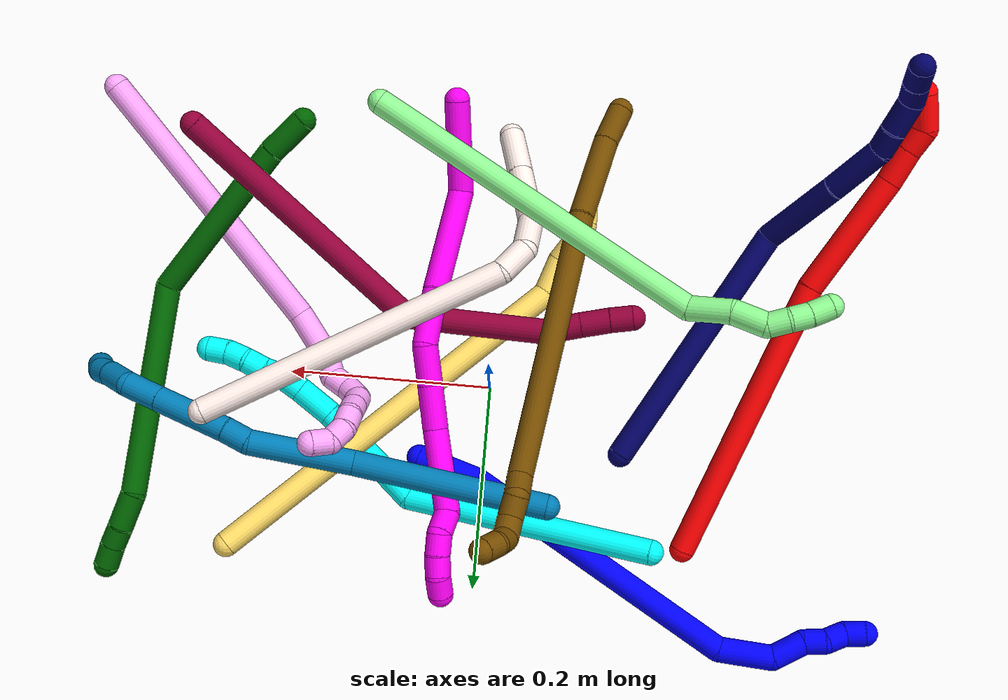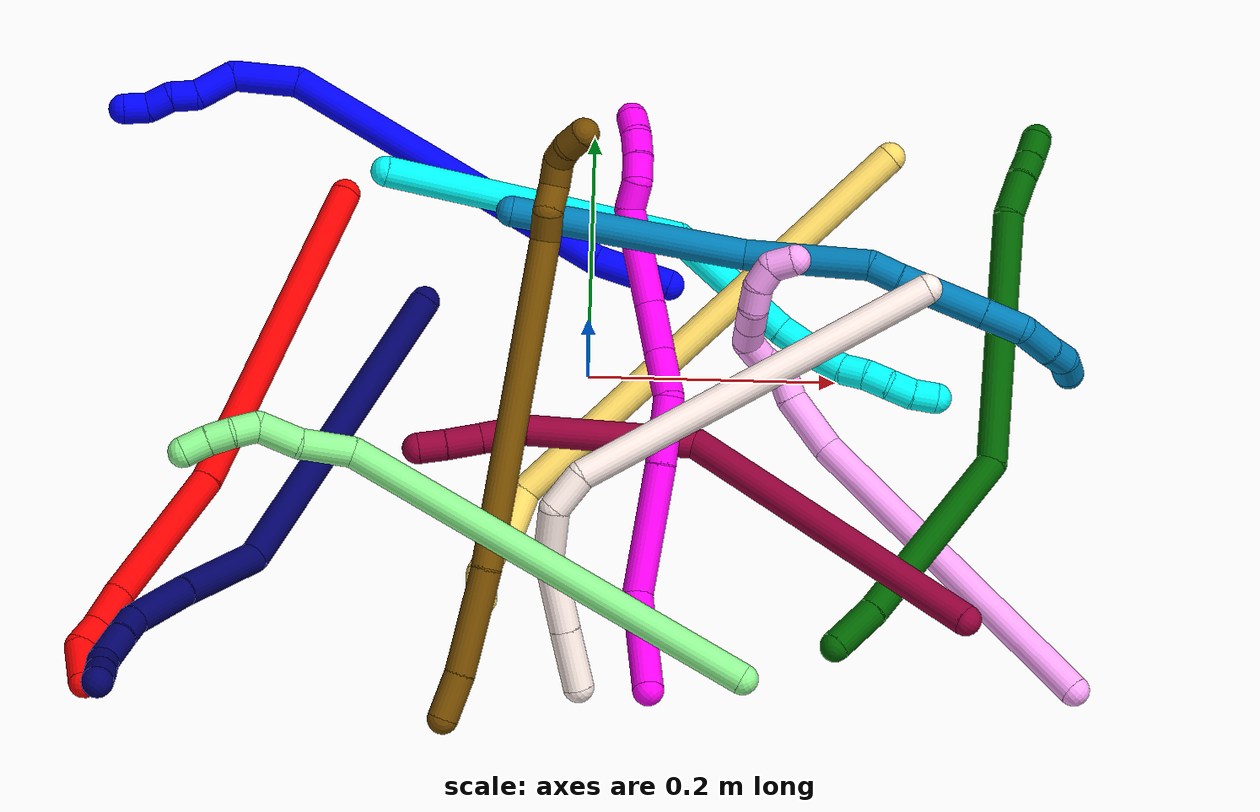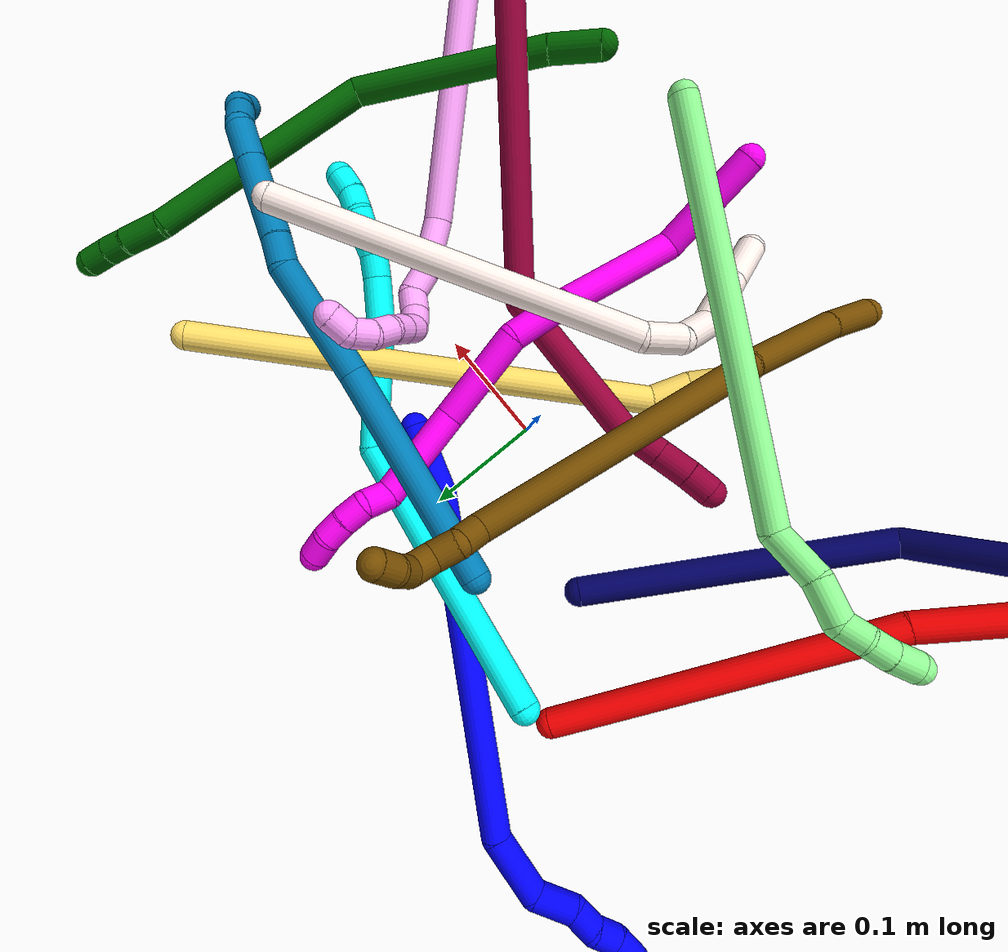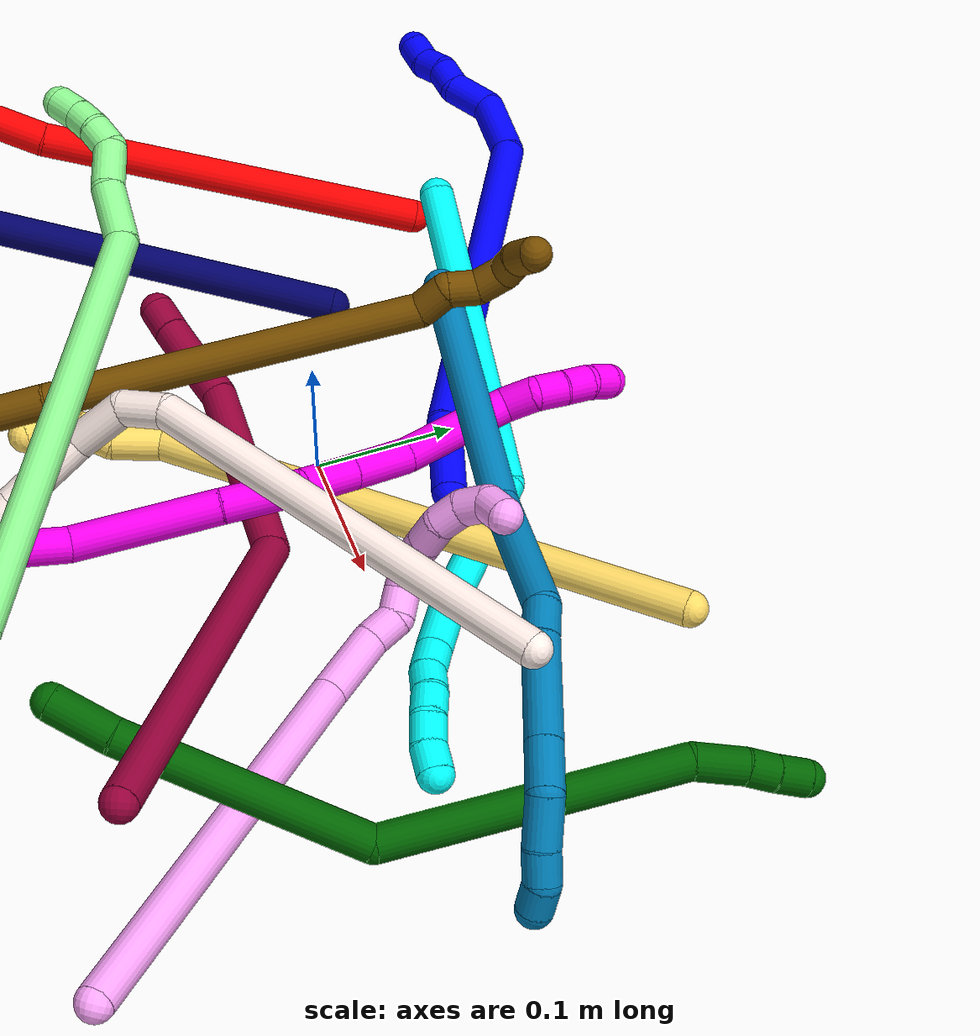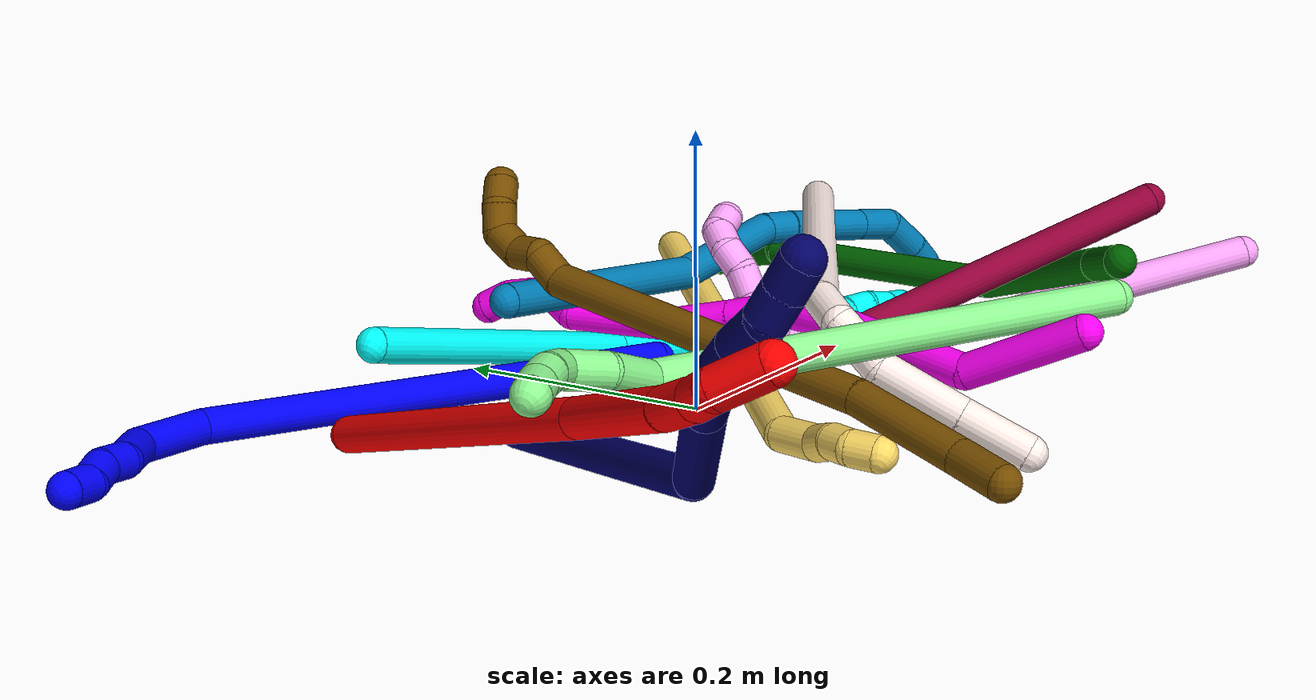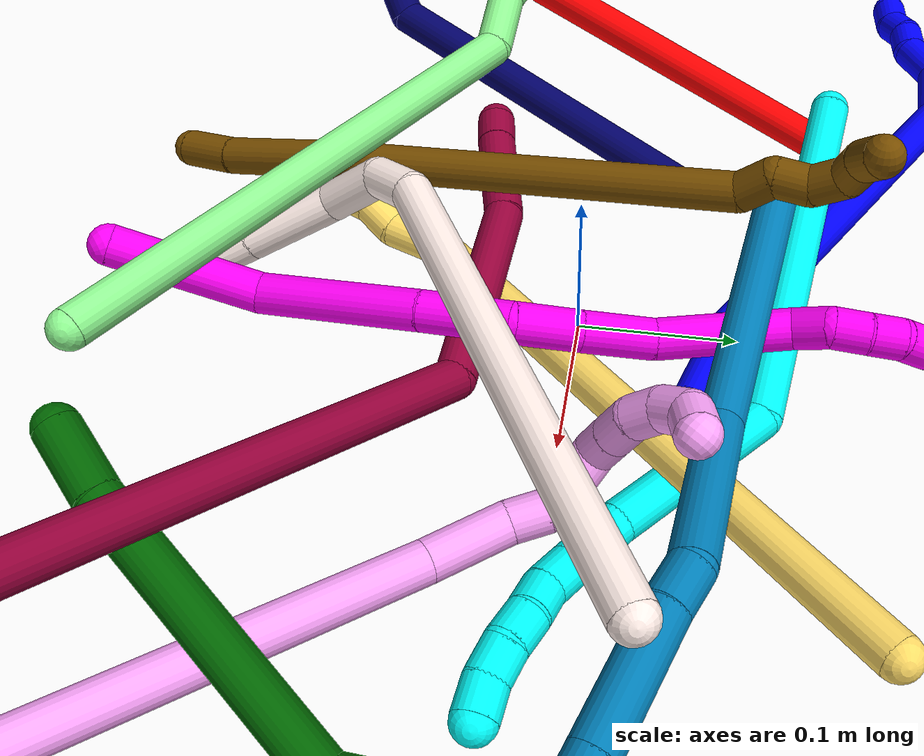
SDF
<sdf version="1.7">
 <world name="default">
  <plugin name="TubeGeneratorPlugin" filename="libtube_generator_plugin.so"/>
  <model name="photoneo_s_sensor">
   <static>1</static>
   <pose>0 0 2 1.57079 1.57079 3.14159</pose>
   <link name="link">
    <inertial><mass>0.1</mass></inertial>
    <sensor name="sensor" type="depth">
     <update_rate>30</update_rate>
     <camera>
      <horizontal_fov>1.22</horizontal_fov>
      <image><width>1920</width><height>1200</height><format>B8G8R8</format></image>
      <clip><near>0.1</near><far>4</far></clip>
      <depth_camera><output>points</output></depth_camera>
     </camera>
     <plugin name="camera_plugin" filename="libgazebo_ros_depth_camera.so">
      <baseline>0.2</baseline>
      <alwaysOn>1</alwaysOn>
      <updateRate>0.0</updateRate>
      <cameraName>camera_ir</cameraName>
      <imageTopicName>/camera/color/image_raw</imageTopicName>
      <cameraInfoTopicName>/camera/color/camera_info</cameraInfoTopicName>
      <depthImageTopicName>/camera/depth/image_raw</depthImageTopicName>
      <depthImageCameraInfoTopicName>/camera/depth/camera_info</depthImageCameraInfoTopicName>
      <pointCloudTopicName>/camera/depth/points</pointCloudTopicName>
      <frameName>fr_optical</frameName>
      <pointCloudCutoff>0.1</pointCloudCutoff>
      <pointCloudCutoffMax>2.0</pointCloudCutoffMax>
      <distortionK1>0</distortionK1>
      <distortionK2>0</distortionK2>
      <distortionK3>0</distortionK3>
      <distortionT1>0</distortionT1>
      <distortionT2>0</distortionT2>
      <CxPrime>0</CxPrime>
      <Cx>0</Cx>
      <Cy>0</Cy>
      <focalLength>0</focalLength>
      <hackBaseline>0</hackBaseline>
     </plugin>
    </sensor>
   </link>
  </model>
  <gravity>0 0 -9.8</gravity>
  <magnetic_field>6e-06 2.3e-05 -4.2e-05</magnetic_field>
  <atmosphere type="adiabatic"/>
  <physics name="default_physics" default="0" type="ode">
   <max_step_size>0.003</max_step_size>
   <real_time_factor>1</real_time_factor>
   <real_time_update_rate>1000</real_time_update_rate>
   <max_contacts>10000</max_contacts>
   <ode>
    <solver>
     <type>quick</type>
     <iters>100</iters>
     <sor>1.3</sor>
     <use_dynamic_moi_rescaling>0</use_dynamic_moi_rescaling>
    </solver>
    <constraints>
     <contact_max_correcting_vel>0</contact_max_correcting_vel>
     <contact_surface_layer>0.001</contact_surface_layer>
     <cfm>0</cfm>
     <erp>0.2</erp>
    </constraints>
   </ode>
  </physics>
  <scene><ambient>0.4 0.4 0.4 1</ambient><background>0.7 0.7 0.7 1</background><shadows>0</shadows></scene>
  <audio><device>default</device></audio>
  <spherical_coordinates>
   <surface_model>EARTH_WGS84</surface_model>
   <latitude_deg>0</latitude_deg>
   <longitude_deg>0</longitude_deg>
   <elevation>0</elevation>
   <heading_deg>0</heading_deg>
  </spherical_coordinates>
  <model name="bin">
   <static>1</static>
   <link name="bottom">
    <collision name="collision-bottom">
     <pose>0 0 -0.01 0 -0 0</pose>
     <geometry><box><size>0.8 0.6 0.02</size></box></geometry>
     <surface>
      <friction><ode><mu>100</mu><mu2>100</mu2></ode></friction>
      <contact><collide_bitmask>65535</collide_bitmask></contact>
     </surface>
    </collision>
   </link>
   <link name="west_wall">
    <collision name="collision-west_wall">
     <pose>-0.41 0 0.1 0 -0 0</pose>
     <geometry><box><size>0.02 0.6 0.2</size></box></geometry>
     <surface>
      <friction><ode><mu>100</mu><mu2>100</mu2></ode></friction>
      <contact><collide_bitmask>65535</collide_bitmask></contact>
     </surface>
    </collision>
   </link>
   <link name="east_wall">
    <collision name="collision-east_wall">
     <pose>0.41 0 0.1 0 -0 0</pose>
     <geometry><box><size>0.02 0.6 0.2</size></box></geometry>
     <surface>
      <friction><ode><mu>100</mu><mu2>100</mu2></ode></friction>
      <contact><collide_bitmask>65535</collide_bitmask></contact>
     </surface>
    </collision>
   </link>
   <link name="south_wall">
    <collision name="collision-south_wall">
     <pose>0 -0.31 0.1 0 -0 0</pose>
     <geometry><box><size>0.8 0.02 0.2</size></box></geometry>
     <surface>
      <friction><ode><mu>100</mu><mu2>100</mu2></ode></friction>
      <contact><collide_bitmask>65535</collide_bitmask></contact>
     </surface>
    </collision>
   </link>
   <link name="north_wall">
    <collision name="collision-north_wall">
     <pose>0 0.31 0.1 0 -0 0</pose>
     <geometry><box><size>0.8 0.02 0.2</size></box></geometry>
     <surface>
      <friction><ode><mu>100</mu><mu2>100</mu2></ode></friction>
      <contact><collide_bitmask>65535</collide_bitmask></contact>
     </surface>
    </collision>
   </link>
  </model>
  <model name="1">
   <static>0</static>
   <link name="1">
    <collision name="collision-cylinder-e_1_1_4">
     <pose>-0.004019 0.009204 0.029469 -0.302724 -0.129452 0.019772</pose>
     <geometry><cylinder><radius>0.0125</radius><length>0.062266</length></cylinder></geometry>
     <surface>
      <friction><ode><mu>1.16</mu><mu2>1.16</mu2><slip1>0</slip1><slip2>0</slip2></ode></friction>
      <contact><ode><kp>1e+06</kp><kd>1</kd><max_vel>0</max_vel><min_depth>0.001</min_depth></ode></contact>
     </surface>
    </collision>
    <visual name="visual-cylinder-e_1_1_4">
     <pose>-0.004019 0.009204 0.029469 -0.302724 -0.129452 0.019772</pose>
     <geometry><cylinder><radius>0.0125</radius><length>0.062266</length></cylinder></geometry>
     <material><ambient>0 0 1 1</ambient></material>
    </visual>
    <collision name="collision-cylinder-e_2_4_5">
     <pose>-0.058876 0.065907 0.184811 -0.360834 -0.361289 0.066601</pose>
     <geometry><cylinder><radius>0.0125</radius><length>0.287644</length></cylinder></geometry>
     <surface>
      <friction><ode><mu>1.16</mu><mu2>1.16</mu2><slip1>0</slip1><slip2>0</slip2></ode></friction>
      <contact><ode><kp>1e+06</kp><kd>1</kd><max_vel>0</max_vel><min_depth>0.001</min_depth></ode></contact>
     </surface>
    </collision>
    <visual name="visual-cylinder-e_2_4_5">
     <pose>-0.058876 0.065907 0.184811 -0.360834 -0.361289 0.066601</pose>
     <geometry><cylinder><radius>0.0125</radius><length>0.287644</length></cylinder></geometry>
     <material><ambient>0 0 1 1</ambient></material>
    </visual>
    <collision name="collision-cylinder-e_3_5_6">
     <pose>-0.108482 0.117528 0.33723 -0.15406 0.045853 -0.00354</pose>
     <geometry><cylinder><radius>0.0125</radius><length>0.053785</length></cylinder></geometry>
     <surface>
      <friction><ode><mu>1.16</mu><mu2>1.16</mu2><slip1>0</slip1><slip2>0</slip2></ode></friction>
      <contact><ode><kp>1e+06</kp><kd>1</kd><max_vel>0</max_vel><min_depth>0.001</min_depth></ode></contact>
     </surface>
    </collision>
    <visual name="visual-cylinder-e_3_5_6">
     <pose>-0.108482 0.117528 0.33723 -0.15406 0.045853 -0.00354</pose>
     <geometry><cylinder><radius>0.0125</radius><length>0.053785</length></cylinder></geometry>
     <material><ambient>0 0 1 1</ambient></material>
    </visual>
    <collision name="collision-cylinder-e_4_6_7">
     <pose>-0.097515 0.11961 0.377688 0.145587 0.605524 0.045549</pose>
     <geometry><cylinder><radius>0.0125</radius><length>0.034203</length></cylinder></geometry>
     <surface>
      <friction><ode><mu>1.16</mu><mu2>1.16</mu2><slip1>0</slip1><slip2>0</slip2></ode></friction>
      <contact><ode><kp>1e+06</kp><kd>1</kd><max_vel>0</max_vel><min_depth>0.001</min_depth></ode></contact>
     </surface>
    </collision>
    <visual name="visual-cylinder-e_4_6_7">
     <pose>-0.097515 0.11961 0.377688 0.145587 0.605524 0.045549</pose>
     <geometry><cylinder><radius>0.0125</radius><length>0.034203</length></cylinder></geometry>
     <material><ambient>0 0 1 1</ambient></material>
    </visual>
    <collision name="collision-cylinder-e_5_7_8">
     <pose>-0.085176 0.119004 0.401732 -0.140583 0.249302 -0.017644</pose>
     <geometry><cylinder><radius>0.0125</radius><length>0.021117</length></cylinder></geometry>
     <surface>
      <friction><ode><mu>1.16</mu><mu2>1.16</mu2><slip1>0</slip1><slip2>0</slip2></ode></friction>
      <contact><ode><kp>1e+06</kp><kd>1</kd><max_vel>0</max_vel><min_depth>0.001</min_depth></ode></contact>
     </surface>
    </collision>
    <visual name="visual-cylinder-e_5_7_8">
     <pose>-0.085176 0.119004 0.401732 -0.140583 0.249302 -0.017644</pose>
     <geometry><cylinder><radius>0.0125</radius><length>0.021117</length></cylinder></geometry>
     <material><ambient>0 0 1 1</ambient></material>
    </visual>
    <collision name="collision-cylinder-e_6_8_9">
     <pose>-0.07871 0.117719 0.421002 0.289175 0.384765 0.05671</pose>
     <geometry><cylinder><radius>0.0125</radius><length>0.020572</length></cylinder></geometry>
     <surface>
      <friction><ode><mu>1.16</mu><mu2>1.16</mu2><slip1>0</slip1><slip2>0</slip2></ode></friction>
      <contact><ode><kp>1e+06</kp><kd>1</kd><max_vel>0</max_vel><min_depth>0.001</min_depth></ode></contact>
     </surface>
    </collision>
    <visual name="visual-cylinder-e_6_8_9">
     <pose>-0.07871 0.117719 0.421002 0.289175 0.384765 0.05671</pose>
     <geometry><cylinder><radius>0.0125</radius><length>0.020572</length></cylinder></geometry>
     <material><ambient>0 0 1 1</ambient></material>
    </visual>
    <collision name="collision-cylinder-e_7_9_2">
     <pose>-0.072576 0.116217 0.440015 -0.122559 0.224616 -0.01384</pose>
     <geometry><cylinder><radius>0.0125</radius><length>0.020412</length></cylinder></geometry>
     <surface>
      <friction><ode><mu>1.16</mu><mu2>1.16</mu2><slip1>0</slip1><slip2>0</slip2></ode></friction>
      <contact><ode><kp>1e+06</kp><kd>1</kd><max_vel>0</max_vel><min_depth>0.001</min_depth></ode></contact>
     </surface>
    </collision>
    <visual name="visual-cylinder-e_7_9_2">
     <pose>-0.072576 0.116217 0.440015 -0.122559 0.224616 -0.01384</pose>
     <geometry><cylinder><radius>0.0125</radius><length>0.020412</length></cylinder></geometry>
     <material><ambient>0 0 1 1</ambient></material>
    </visual>
    <collision name="collision-sphere-2">
     <pose>-0.070303 0.117433 0.44989 0 -0 0</pose>
     <geometry><sphere><radius>0.0125</radius></sphere></geometry>
     <surface>
      <friction><ode><mu>1.16</mu><mu2>1.16</mu2><slip1>0</slip1><slip2>0</slip2></ode></friction>
      <contact><ode><kp>1e+06</kp><kd>1</kd><max_vel>0</max_vel><min_depth>0.001</min_depth></ode></contact>
     </surface>
    </collision>
    <visual name="visual-sphere-2">
     <pose>-0.070303 0.117433 0.44989 0 -0 0</pose>
     <geometry><sphere><radius>0.0125</radius></sphere></geometry>
     <material><ambient>0 0 1 1</ambient></material>
    </visual>
    <collision name="collision-sphere-9">
     <pose>-0.074849 0.115 0.43014 0 -0 0</pose>
     <geometry><sphere><radius>0.0125</radius></sphere></geometry>
     <surface>
      <friction><ode><mu>1.16</mu><mu2>1.16</mu2><slip1>0</slip1><slip2>0</slip2></ode></friction>
      <contact><ode><kp>1e+06</kp><kd>1</kd><max_vel>0</max_vel><min_depth>0.001</min_depth></ode></contact>
     </surface>
    </collision>
    <visual name="visual-sphere-9">
     <pose>-0.074849 0.115 0.43014 0 -0 0</pose>
     <geometry><sphere><radius>0.0125</radius></sphere></geometry>
     <material><ambient>0 0 1 1</ambient></material>
    </visual>
    <collision name="collision-sphere-4">
     <pose>-0.008038 0.018408 0.058938 0 -0 0</pose>
     <geometry><sphere><radius>0.0125</radius></sphere></geometry>
     <surface>
      <friction><ode><mu>1.16</mu><mu2>1.16</mu2><slip1>0</slip1><slip2>0</slip2></ode></friction>
      <contact><ode><kp>1e+06</kp><kd>1</kd><max_vel>0</max_vel><min_depth>0.001</min_depth></ode></contact>
     </surface>
    </collision>
    <visual name="visual-sphere-4">
     <pose>-0.008038 0.018408 0.058938 0 -0 0</pose>
     <geometry><sphere><radius>0.0125</radius></sphere></geometry>
     <material><ambient>0 0 1 1</ambient></material>
    </visual>
    <collision name="collision-sphere-1">
     <geometry><sphere><radius>0.0125</radius></sphere></geometry>
     <surface>
      <friction><ode><mu>1.16</mu><mu2>1.16</mu2><slip1>0</slip1><slip2>0</slip2></ode></friction>
      <contact><ode><kp>1e+06</kp><kd>1</kd><max_vel>0</max_vel><min_depth>0.001</min_depth></ode></contact>
     </surface>
    </collision>
    <visual name="visual-sphere-1">
     <geometry><sphere><radius>0.0125</radius></sphere></geometry>
     <material><ambient>0 0 1 1</ambient></material>
    </visual>
    <collision name="collision-sphere-8">
     <pose>-0.082571 0.120438 0.411863 0 -0 0</pose>
     <geometry><sphere><radius>0.0125</radius></sphere></geometry>
     <surface>
      <friction><ode><mu>1.16</mu><mu2>1.16</mu2><slip1>0</slip1><slip2>0</slip2></ode></friction>
      <contact><ode><kp>1e+06</kp><kd>1</kd><max_vel>0</max_vel><min_depth>0.001</min_depth></ode></contact>
     </surface>
    </collision>
    <visual name="visual-sphere-8">
     <pose>-0.082571 0.120438 0.411863 0 -0 0</pose>
     <geometry><sphere><radius>0.0125</radius></sphere></geometry>
     <material><ambient>0 0 1 1</ambient></material>
    </visual>
    <collision name="collision-sphere-5">
     <pose>-0.109715 0.113406 0.310684 0 -0 0</pose>
     <geometry><sphere><radius>0.0125</radius></sphere></geometry>
     <surface>
      <friction><ode><mu>1.16</mu><mu2>1.16</mu2><slip1>0</slip1><slip2>0</slip2></ode></friction>
      <contact><ode><kp>1e+06</kp><kd>1</kd><max_vel>0</max_vel><min_depth>0.001</min_depth></ode></contact>
     </surface>
    </collision>
    <visual name="visual-sphere-5">
     <pose>-0.109715 0.113406 0.310684 0 -0 0</pose>
     <geometry><sphere><radius>0.0125</radius></sphere></geometry>
     <material><ambient>0 0 1 1</ambient></material>
    </visual>
    <collision name="collision-sphere-6">
     <pose>-0.107249 0.12165 0.363776 0 -0 0</pose>
     <geometry><sphere><radius>0.0125</radius></sphere></geometry>
     <surface>
      <friction><ode><mu>1.16</mu><mu2>1.16</mu2><slip1>0</slip1><slip2>0</slip2></ode></friction>
      <contact><ode><kp>1e+06</kp><kd>1</kd><max_vel>0</max_vel><min_depth>0.001</min_depth></ode></contact>
     </surface>
    </collision>
    <visual name="visual-sphere-6">
     <pose>-0.107249 0.12165 0.363776 0 -0 0</pose>
     <geometry><sphere><radius>0.0125</radius></sphere></geometry>
     <material><ambient>0 0 1 1</ambient></material>
    </visual>
    <collision name="collision-sphere-7">
     <pose>-0.087781 0.11757 0.391601 0 -0 0</pose>
     <geometry><sphere><radius>0.0125</radius></sphere></geometry>
     <surface>
      <friction><ode><mu>1.16</mu><mu2>1.16</mu2><slip1>0</slip1><slip2>0</slip2></ode></friction>
      <contact><ode><kp>1e+06</kp><kd>1</kd><max_vel>0</max_vel><min_depth>0.001</min_depth></ode></contact>
     </surface>
    </collision>
    <visual name="visual-sphere-7">
     <pose>-0.087781 0.11757 0.391601 0 -0 0</pose>
     <geometry><sphere><radius>0.0125</radius></sphere></geometry>
     <material><ambient>0 0 1 1</ambient></material>
    </visual>
    <inertial>
     <pose>-0.06251 0.0745 0.224354 0 -0 0</pose>
     <mass>0.5</mass>
     <inertia>
      <ixx>0.002027</ixx>
      <ixy>0</ixy>
      <ixz>0</ixz>
      <iyy>0.002058</iyy>
      <iyz>0</iyz>
      <izz>7.1e-05</izz>
     </inertia>
    </inertial>
   </link>
   <pose>0.063472 0.075536 0.011552 1.74061 -0.489316 -1.69049</pose>
  </model>
  <model name="2">
   <static>0</static>
   <link name="2">
    <collision name="collision-cylinder-e_1_1_4">
     <pose>-0.022684 -0.051345 0.1313 0.372766 -0.159534 -0.030145</pose>
     <geometry><cylinder><radius>0.0125</radius><length>0.28559</length></cylinder></geometry>
     <surface>
      <friction><ode><mu>1.16</mu><mu2>1.16</mu2><slip1>0</slip1><slip2>0</slip2></ode></friction>
      <contact><ode><kp>1e+06</kp><kd>1</kd><max_vel>0</max_vel><min_depth>0.001</min_depth></ode></contact>
     </surface>
    </collision>
    <visual name="visual-cylinder-e_1_1_4">
     <pose>-0.022684 -0.051345 0.1313 0.372766 -0.159534 -0.030145</pose>
     <geometry><cylinder><radius>0.0125</radius><length>0.28559</length></cylinder></geometry>
     <material><ambient>1 0 0 1</ambient></material>
    </visual>
    <collision name="collision-cylinder-e_2_4_5">
     <pose>-0.051687 -0.134677 0.314356 0.553578 -0.103472 -0.029419</pose>
     <geometry><cylinder><radius>0.0125</radius><length>0.122342</length></cylinder></geometry>
     <surface>
      <friction><ode><mu>1.16</mu><mu2>1.16</mu2><slip1>0</slip1><slip2>0</slip2></ode></friction>
      <contact><ode><kp>1e+06</kp><kd>1</kd><max_vel>0</max_vel><min_depth>0.001</min_depth></ode></contact>
     </surface>
    </collision>
    <visual name="visual-cylinder-e_2_4_5">
     <pose>-0.051687 -0.134677 0.314356 0.553578 -0.103472 -0.029419</pose>
     <geometry><cylinder><radius>0.0125</radius><length>0.122342</length></cylinder></geometry>
     <material><ambient>1 0 0 1</ambient></material>
    </visual>
    <collision name="collision-cylinder-e_3_5_6">
     <pose>-0.061734 -0.174829 0.380631 0.512264 -0.220252 -0.057899</pose>
     <geometry><cylinder><radius>0.0125</radius><length>0.034137</length></cylinder></geometry>
     <surface>
      <friction><ode><mu>1.16</mu><mu2>1.16</mu2><slip1>0</slip1><slip2>0</slip2></ode></friction>
      <contact><ode><kp>1e+06</kp><kd>1</kd><max_vel>0</max_vel><min_depth>0.001</min_depth></ode></contact>
     </surface>
    </collision>
    <visual name="visual-cylinder-e_3_5_6">
     <pose>-0.061734 -0.174829 0.380631 0.512264 -0.220252 -0.057899</pose>
     <geometry><cylinder><radius>0.0125</radius><length>0.034137</length></cylinder></geometry>
     <material><ambient>1 0 0 1</ambient></material>
    </visual>
    <collision name="collision-cylinder-e_4_6_7">
     <pose>-0.06829 -0.189865 0.404295 0.644454 -0.242257 -0.081234</pose>
     <geometry><cylinder><radius>0.0125</radius><length>0.023568</length></cylinder></geometry>
     <surface>
      <friction><ode><mu>1.16</mu><mu2>1.16</mu2><slip1>0</slip1><slip2>0</slip2></ode></friction>
      <contact><ode><kp>1e+06</kp><kd>1</kd><max_vel>0</max_vel><min_depth>0.001</min_depth></ode></contact>
     </surface>
    </collision>
    <visual name="visual-cylinder-e_4_6_7">
     <pose>-0.06829 -0.189865 0.404295 0.644454 -0.242257 -0.081234</pose>
     <geometry><cylinder><radius>0.0125</radius><length>0.023568</length></cylinder></geometry>
     <material><ambient>1 0 0 1</ambient></material>
    </visual>
    <collision name="collision-cylinder-e_5_7_2">
     <pose>-0.080766 -0.19669 0.427656 -0.003387 -0.596364 0.001041</pose>
     <geometry><cylinder><radius>0.0125</radius><length>0.034362</length></cylinder></geometry>
     <surface>
      <friction><ode><mu>1.16</mu><mu2>1.16</mu2><slip1>0</slip1><slip2>0</slip2></ode></friction>
      <contact><ode><kp>1e+06</kp><kd>1</kd><max_vel>0</max_vel><min_depth>0.001</min_depth></ode></contact>
     </surface>
    </collision>
    <visual name="visual-cylinder-e_5_7_2">
     <pose>-0.080766 -0.19669 0.427656 -0.003387 -0.596364 0.001041</pose>
     <geometry><cylinder><radius>0.0125</radius><length>0.034362</length></cylinder></geometry>
     <material><ambient>1 0 0 1</ambient></material>
    </visual>
    <collision name="collision-sphere-2">
     <pose>-0.090416 -0.196642 0.441871 0 -0 0</pose>
     <geometry><sphere><radius>0.0125</radius></sphere></geometry>
     <surface>
      <friction><ode><mu>1.16</mu><mu2>1.16</mu2><slip1>0</slip1><slip2>0</slip2></ode></friction>
      <contact><ode><kp>1e+06</kp><kd>1</kd><max_vel>0</max_vel><min_depth>0.001</min_depth></ode></contact>
     </surface>
    </collision>
    <visual name="visual-sphere-2">
     <pose>-0.090416 -0.196642 0.441871 0 -0 0</pose>
     <geometry><sphere><radius>0.0125</radius></sphere></geometry>
     <material><ambient>1 0 0 1</ambient></material>
    </visual>
    <collision name="collision-sphere-7">
     <pose>-0.071117 -0.196738 0.41344 0 -0 0</pose>
     <geometry><sphere><radius>0.0125</radius></sphere></geometry>
     <surface>
      <friction><ode><mu>1.16</mu><mu2>1.16</mu2><slip1>0</slip1><slip2>0</slip2></ode></friction>
      <contact><ode><kp>1e+06</kp><kd>1</kd><max_vel>0</max_vel><min_depth>0.001</min_depth></ode></contact>
     </surface>
    </collision>
    <visual name="visual-sphere-7">
     <pose>-0.071117 -0.196738 0.41344 0 -0 0</pose>
     <geometry><sphere><radius>0.0125</radius></sphere></geometry>
     <material><ambient>1 0 0 1</ambient></material>
    </visual>
    <collision name="collision-sphere-6">
     <pose>-0.065463 -0.182993 0.395149 0 -0 0</pose>
     <geometry><sphere><radius>0.0125</radius></sphere></geometry>
     <surface>
      <friction><ode><mu>1.16</mu><mu2>1.16</mu2><slip1>0</slip1><slip2>0</slip2></ode></friction>
      <contact><ode><kp>1e+06</kp><kd>1</kd><max_vel>0</max_vel><min_depth>0.001</min_depth></ode></contact>
     </surface>
    </collision>
    <visual name="visual-sphere-6">
     <pose>-0.065463 -0.182993 0.395149 0 -0 0</pose>
     <geometry><sphere><radius>0.0125</radius></sphere></geometry>
     <material><ambient>1 0 0 1</ambient></material>
    </visual>
    <collision name="collision-sphere-5">
     <pose>-0.058005 -0.166665 0.366113 0 -0 0</pose>
     <geometry><sphere><radius>0.0125</radius></sphere></geometry>
     <surface>
      <friction><ode><mu>1.16</mu><mu2>1.16</mu2><slip1>0</slip1><slip2>0</slip2></ode></friction>
      <contact><ode><kp>1e+06</kp><kd>1</kd><max_vel>0</max_vel><min_depth>0.001</min_depth></ode></contact>
     </surface>
    </collision>
    <visual name="visual-sphere-5">
     <pose>-0.058005 -0.166665 0.366113 0 -0 0</pose>
     <geometry><sphere><radius>0.0125</radius></sphere></geometry>
     <material><ambient>1 0 0 1</ambient></material>
    </visual>
    <collision name="collision-sphere-1">
     <geometry><sphere><radius>0.0125</radius></sphere></geometry>
     <surface>
      <friction><ode><mu>1.16</mu><mu2>1.16</mu2><slip1>0</slip1><slip2>0</slip2></ode></friction>
      <contact><ode><kp>1e+06</kp><kd>1</kd><max_vel>0</max_vel><min_depth>0.001</min_depth></ode></contact>
     </surface>
    </collision>
    <visual name="visual-sphere-1">
     <geometry><sphere><radius>0.0125</radius></sphere></geometry>
     <material><ambient>1 0 0 1</ambient></material>
    </visual>
    <collision name="collision-sphere-4">
     <pose>-0.045368 -0.102689 0.262599 0 -0 0</pose>
     <geometry><sphere><radius>0.0125</radius></sphere></geometry>
     <surface>
      <friction><ode><mu>1.16</mu><mu2>1.16</mu2><slip1>0</slip1><slip2>0</slip2></ode></friction>
      <contact><ode><kp>1e+06</kp><kd>1</kd><max_vel>0</max_vel><min_depth>0.001</min_depth></ode></contact>
     </surface>
    </collision>
    <visual name="visual-sphere-4">
     <pose>-0.045368 -0.102689 0.262599 0 -0 0</pose>
     <geometry><sphere><radius>0.0125</radius></sphere></geometry>
     <material><ambient>1 0 0 1</ambient></material>
    </visual>
    <inertial>
     <pose>-0.038588 -0.096684 0.226349 0 -0 0</pose>
     <mass>0.5</mass>
     <inertia>
      <ixx>0.002023</ixx>
      <ixy>0</ixy>
      <ixz>0</ixz>
      <iyy>0.001887</iyy>
      <iyz>0</iyz>
      <izz>0.001153</izz>
     </inertia>
    </inertial>
   </link>
   <pose>-0.202894 0.144289 0.011514 -1.64848 1.08418 2.97499</pose>
  </model>
  <model name="3">
   <static>0</static>
   <link name="3">
    <collision name="collision-cylinder-e_1_1_4">
     <pose>0.096482 -0.000642 0.076284 0.008417 0.901764 0.004075</pose>
     <geometry><cylinder><radius>0.0125</radius><length>0.245995</length></cylinder></geometry>
     <surface>
      <friction><ode><mu>1.16</mu><mu2>1.16</mu2><slip1>0</slip1><slip2>0</slip2></ode></friction>
      <contact><ode><kp>1e+06</kp><kd>1</kd><max_vel>0</max_vel><min_depth>0.001</min_depth></ode></contact>
     </surface>
    </collision>
    <visual name="visual-cylinder-e_1_1_4">
     <pose>0.096482 -0.000642 0.076284 0.008417 0.901764 0.004075</pose>
     <geometry><cylinder><radius>0.0125</radius><length>0.245995</length></cylinder></geometry>
     <material><ambient>0.003922 1 0.996078 1</ambient></material>
    </visual>
    <collision name="collision-cylinder-e_2_4_5">
     <pose>0.226203 -0.033844 0.185129 0.785362 0.625242 0.266168</pose>
     <geometry><cylinder><radius>0.0125</radius><length>0.113583</length></cylinder></geometry>
     <surface>
      <friction><ode><mu>1.16</mu><mu2>1.16</mu2><slip1>0</slip1><slip2>0</slip2></ode></friction>
      <contact><ode><kp>1e+06</kp><kd>1</kd><max_vel>0</max_vel><min_depth>0.001</min_depth></ode></contact>
     </surface>
    </collision>
    <visual name="visual-cylinder-e_2_4_5">
     <pose>0.226203 -0.033844 0.185129 0.785362 0.625242 0.266168</pose>
     <geometry><cylinder><radius>0.0125</radius><length>0.113583</length></cylinder></geometry>
     <material><ambient>0.003922 1 0.996078 1</ambient></material>
    </visual>
    <collision name="collision-cylinder-e_3_5_6">
     <pose>0.270603 -0.075603 0.230604 0.619013 0.613336 0.201836</pose>
     <geometry><cylinder><radius>0.0125</radius><length>0.038778</length></cylinder></geometry>
     <surface>
      <friction><ode><mu>1.16</mu><mu2>1.16</mu2><slip1>0</slip1><slip2>0</slip2></ode></friction>
      <contact><ode><kp>1e+06</kp><kd>1</kd><max_vel>0</max_vel><min_depth>0.001</min_depth></ode></contact>
     </surface>
    </collision>
    <visual name="visual-cylinder-e_3_5_6">
     <pose>0.270603 -0.075603 0.230604 0.619013 0.613336 0.201836</pose>
     <geometry><cylinder><radius>0.0125</radius><length>0.038778</length></cylinder></geometry>
     <material><ambient>0.003922 1 0.996078 1</ambient></material>
    </visual>
    <collision name="collision-cylinder-e_4_6_7">
     <pose>0.286749 -0.089472 0.251721 0.517448 0.485894 0.130998</pose>
     <geometry><cylinder><radius>0.0125</radius><length>0.02135</length></cylinder></geometry>
     <surface>
      <friction><ode><mu>1.16</mu><mu2>1.16</mu2><slip1>0</slip1><slip2>0</slip2></ode></friction>
      <contact><ode><kp>1e+06</kp><kd>1</kd><max_vel>0</max_vel><min_depth>0.001</min_depth></ode></contact>
     </surface>
    </collision>
    <visual name="visual-cylinder-e_4_6_7">
     <pose>0.286749 -0.089472 0.251721 0.517448 0.485894 0.130998</pose>
     <geometry><cylinder><radius>0.0125</radius><length>0.02135</length></cylinder></geometry>
     <material><ambient>0.003922 1 0.996078 1</ambient></material>
    </visual>
    <collision name="collision-cylinder-e_5_7_8">
     <pose>0.29616 -0.096088 0.268713 0.218029 0.456961 0.050892</pose>
     <geometry><cylinder><radius>0.0125</radius><length>0.02006</length></cylinder></geometry>
     <surface>
      <friction><ode><mu>1.16</mu><mu2>1.16</mu2><slip1>0</slip1><slip2>0</slip2></ode></friction>
      <contact><ode><kp>1e+06</kp><kd>1</kd><max_vel>0</max_vel><min_depth>0.001</min_depth></ode></contact>
     </surface>
    </collision>
    <visual name="visual-cylinder-e_5_7_8">
     <pose>0.29616 -0.096088 0.268713 0.218029 0.456961 0.050892</pose>
     <geometry><cylinder><radius>0.0125</radius><length>0.02006</length></cylinder></geometry>
     <material><ambient>0.003922 1 0.996078 1</ambient></material>
    </visual>
    <collision name="collision-cylinder-e_6_8_9">
     <pose>0.306447 -0.101064 0.285089 0.379769 0.622323 0.123469</pose>
     <geometry><cylinder><radius>0.0125</radius><length>0.020112</length></cylinder></geometry>
     <surface>
      <friction><ode><mu>1.16</mu><mu2>1.16</mu2><slip1>0</slip1><slip2>0</slip2></ode></friction>
      <contact><ode><kp>1e+06</kp><kd>1</kd><max_vel>0</max_vel><min_depth>0.001</min_depth></ode></contact>
     </surface>
    </collision>
    <visual name="visual-cylinder-e_6_8_9">
     <pose>0.306447 -0.101064 0.285089 0.379769 0.622323 0.123469</pose>
     <geometry><cylinder><radius>0.0125</radius><length>0.020112</length></cylinder></geometry>
     <material><ambient>0.003922 1 0.996078 1</ambient></material>
    </visual>
    <collision name="collision-cylinder-e_7_9_10">
     <pose>0.320039 -0.106099 0.298788 0.317196 0.876863 0.149702</pose>
     <geometry><cylinder><radius>0.0125</radius><length>0.020112</length></cylinder></geometry>
     <surface>
      <friction><ode><mu>1.16</mu><mu2>1.16</mu2><slip1>0</slip1><slip2>0</slip2></ode></friction>
      <contact><ode><kp>1e+06</kp><kd>1</kd><max_vel>0</max_vel><min_depth>0.001</min_depth></ode></contact>
     </surface>
    </collision>
    <visual name="visual-cylinder-e_7_9_10">
     <pose>0.320039 -0.106099 0.298788 0.317196 0.876863 0.149702</pose>
     <geometry><cylinder><radius>0.0125</radius><length>0.020112</length></cylinder></geometry>
     <material><ambient>0.003922 1 0.996078 1</ambient></material>
    </visual>
    <collision name="collision-cylinder-e_8_10_2">
     <pose>0.334935 -0.108042 0.311881 -0.0091 0.798374 -0.003839</pose>
     <geometry><cylinder><radius>0.0125</radius><length>0.02001</length></cylinder></geometry>
     <surface>
      <friction><ode><mu>1.16</mu><mu2>1.16</mu2><slip1>0</slip1><slip2>0</slip2></ode></friction>
      <contact><ode><kp>1e+06</kp><kd>1</kd><max_vel>0</max_vel><min_depth>0.001</min_depth></ode></contact>
     </surface>
    </collision>
    <visual name="visual-cylinder-e_8_10_2">
     <pose>0.334935 -0.108042 0.311881 -0.0091 0.798374 -0.003839</pose>
     <geometry><cylinder><radius>0.0125</radius><length>0.02001</length></cylinder></geometry>
     <material><ambient>0.003922 1 0.996078 1</ambient></material>
    </visual>
    <collision name="collision-sphere-2">
     <pose>0.342101 -0.107978 0.318863 0 -0 0</pose>
     <geometry><sphere><radius>0.0125</radius></sphere></geometry>
     <surface>
      <friction><ode><mu>1.16</mu><mu2>1.16</mu2><slip1>0</slip1><slip2>0</slip2></ode></friction>
      <contact><ode><kp>1e+06</kp><kd>1</kd><max_vel>0</max_vel><min_depth>0.001</min_depth></ode></contact>
     </surface>
    </collision>
    <visual name="visual-sphere-2">
     <pose>0.342101 -0.107978 0.318863 0 -0 0</pose>
     <geometry><sphere><radius>0.0125</radius></sphere></geometry>
     <material><ambient>0.003922 1 0.996078 1</ambient></material>
    </visual>
    <collision name="collision-sphere-10">
     <pose>0.32777 -0.108105 0.304899 0 -0 0</pose>
     <geometry><sphere><radius>0.0125</radius></sphere></geometry>
     <surface>
      <friction><ode><mu>1.16</mu><mu2>1.16</mu2><slip1>0</slip1><slip2>0</slip2></ode></friction>
      <contact><ode><kp>1e+06</kp><kd>1</kd><max_vel>0</max_vel><min_depth>0.001</min_depth></ode></contact>
     </surface>
    </collision>
    <visual name="visual-sphere-10">
     <pose>0.32777 -0.108105 0.304899 0 -0 0</pose>
     <geometry><sphere><radius>0.0125</radius></sphere></geometry>
     <material><ambient>0.003922 1 0.996078 1</ambient></material>
    </visual>
    <collision name="collision-sphere-9">
     <pose>0.312309 -0.104093 0.292678 0 -0 0</pose>
     <geometry><sphere><radius>0.0125</radius></sphere></geometry>
     <surface>
      <friction><ode><mu>1.16</mu><mu2>1.16</mu2><slip1>0</slip1><slip2>0</slip2></ode></friction>
      <contact><ode><kp>1e+06</kp><kd>1</kd><max_vel>0</max_vel><min_depth>0.001</min_depth></ode></contact>
     </surface>
    </collision>
    <visual name="visual-sphere-9">
     <pose>0.312309 -0.104093 0.292678 0 -0 0</pose>
     <geometry><sphere><radius>0.0125</radius></sphere></geometry>
     <material><ambient>0.003922 1 0.996078 1</ambient></material>
    </visual>
    <collision name="collision-sphere-4">
     <pose>0.192964 -0.001284 0.152567 0 -0 0</pose>
     <geometry><sphere><radius>0.0125</radius></sphere></geometry>
     <surface>
      <friction><ode><mu>1.16</mu><mu2>1.16</mu2><slip1>0</slip1><slip2>0</slip2></ode></friction>
      <contact><ode><kp>1e+06</kp><kd>1</kd><max_vel>0</max_vel><min_depth>0.001</min_depth></ode></contact>
     </surface>
    </collision>
    <visual name="visual-sphere-4">
     <pose>0.192964 -0.001284 0.152567 0 -0 0</pose>
     <geometry><sphere><radius>0.0125</radius></sphere></geometry>
     <material><ambient>0.003922 1 0.996078 1</ambient></material>
    </visual>
    <collision name="collision-sphere-1">
     <geometry><sphere><radius>0.0125</radius></sphere></geometry>
     <surface>
      <friction><ode><mu>1.16</mu><mu2>1.16</mu2><slip1>0</slip1><slip2>0</slip2></ode></friction>
      <contact><ode><kp>1e+06</kp><kd>1</kd><max_vel>0</max_vel><min_depth>0.001</min_depth></ode></contact>
     </surface>
    </collision>
    <visual name="visual-sphere-1">
     <geometry><sphere><radius>0.0125</radius></sphere></geometry>
     <material><ambient>0.003922 1 0.996078 1</ambient></material>
    </visual>
    <collision name="collision-sphere-8">
     <pose>0.300585 -0.098035 0.2775 0 -0 0</pose>
     <geometry><sphere><radius>0.0125</radius></sphere></geometry>
     <surface>
      <friction><ode><mu>1.16</mu><mu2>1.16</mu2><slip1>0</slip1><slip2>0</slip2></ode></friction>
      <contact><ode><kp>1e+06</kp><kd>1</kd><max_vel>0</max_vel><min_depth>0.001</min_depth></ode></contact>
     </surface>
    </collision>
    <visual name="visual-sphere-8">
     <pose>0.300585 -0.098035 0.2775 0 -0 0</pose>
     <geometry><sphere><radius>0.0125</radius></sphere></geometry>
     <material><ambient>0.003922 1 0.996078 1</ambient></material>
    </visual>
    <collision name="collision-sphere-5">
     <pose>0.259443 -0.066403 0.217691 0 -0 0</pose>
     <geometry><sphere><radius>0.0125</radius></sphere></geometry>
     <surface>
      <friction><ode><mu>1.16</mu><mu2>1.16</mu2><slip1>0</slip1><slip2>0</slip2></ode></friction>
      <contact><ode><kp>1e+06</kp><kd>1</kd><max_vel>0</max_vel><min_depth>0.001</min_depth></ode></contact>
     </surface>
    </collision>
    <visual name="visual-sphere-5">
     <pose>0.259443 -0.066403 0.217691 0 -0 0</pose>
     <geometry><sphere><radius>0.0125</radius></sphere></geometry>
     <material><ambient>0.003922 1 0.996078 1</ambient></material>
    </visual>
    <collision name="collision-sphere-6">
     <pose>0.281764 -0.084803 0.243518 0 -0 0</pose>
     <geometry><sphere><radius>0.0125</radius></sphere></geometry>
     <surface>
      <friction><ode><mu>1.16</mu><mu2>1.16</mu2><slip1>0</slip1><slip2>0</slip2></ode></friction>
      <contact><ode><kp>1e+06</kp><kd>1</kd><max_vel>0</max_vel><min_depth>0.001</min_depth></ode></contact>
     </surface>
    </collision>
    <visual name="visual-sphere-6">
     <pose>0.281764 -0.084803 0.243518 0 -0 0</pose>
     <geometry><sphere><radius>0.0125</radius></sphere></geometry>
     <material><ambient>0.003922 1 0.996078 1</ambient></material>
    </visual>
    <collision name="collision-sphere-7">
     <pose>0.291734 -0.094141 0.259925 0 -0 0</pose>
     <geometry><sphere><radius>0.0125</radius></sphere></geometry>
     <surface>
      <friction><ode><mu>1.16</mu><mu2>1.16</mu2><slip1>0</slip1><slip2>0</slip2></ode></friction>
      <contact><ode><kp>1e+06</kp><kd>1</kd><max_vel>0</max_vel><min_depth>0.001</min_depth></ode></contact>
     </surface>
    </collision>
    <visual name="visual-sphere-7">
     <pose>0.291734 -0.094141 0.259925 0 -0 0</pose>
     <geometry><sphere><radius>0.0125</radius></sphere></geometry>
     <material><ambient>0.003922 1 0.996078 1</ambient></material>
    </visual>
    <inertial>
     <pose>0.182571 -0.0342 0.154967 0 -0 0</pose>
     <mass>0.5</mass>
     <inertia>
      <ixx>0.000944</ixx>
      <ixy>0</ixy>
      <ixz>0</ixz>
      <iyy>0.001386</iyy>
      <iyz>0</iyz>
      <izz>-0.000954</izz>
     </inertia>
    </inertial>
   </link>
   <pose>-0.167415 0.150552 0.064113 -0.250543 0.872707 -0.298159</pose>
  </model>
  <model name="4">
   <static>0</static>
   <link name="4">
    <collision name="collision-cylinder-e_1_1_4">
     <pose>-0.039292 0.089827 -0.103903 -2.42873 -0.278635 0.720364</pose>
     <geometry><cylinder><radius>0.0125</radius><length>0.285717</length></cylinder></geometry>
     <surface>
      <friction><ode><mu>1.16</mu><mu2>1.16</mu2><slip1>0</slip1><slip2>0</slip2></ode></friction>
      <contact><ode><kp>1e+06</kp><kd>1</kd><max_vel>0</max_vel><min_depth>0.001</min_depth></ode></contact>
     </surface>
    </collision>
    <visual name="visual-cylinder-e_1_1_4">
     <pose>-0.039292 0.089827 -0.103903 -2.42873 -0.278635 0.720364</pose>
     <geometry><cylinder><radius>0.0125</radius><length>0.285717</length></cylinder></geometry>
     <material><ambient>1 0.65098 0.996078 1</ambient></material>
    </visual>
    <collision name="collision-cylinder-e_2_4_5">
     <pose>-0.087136 0.1897 -0.228833 -2.69589 -0.351705 1.32994</pose>
     <geometry><cylinder><radius>0.0125</radius><length>0.049647</length></cylinder></geometry>
     <surface>
      <friction><ode><mu>1.16</mu><mu2>1.16</mu2><slip1>0</slip1><slip2>0</slip2></ode></friction>
      <contact><ode><kp>1e+06</kp><kd>1</kd><max_vel>0</max_vel><min_depth>0.001</min_depth></ode></contact>
     </surface>
    </collision>
    <visual name="visual-cylinder-e_2_4_5">
     <pose>-0.087136 0.1897 -0.228833 -2.69589 -0.351705 1.32994</pose>
     <geometry><cylinder><radius>0.0125</radius><length>0.049647</length></cylinder></geometry>
     <material><ambient>1 0.65098 0.996078 1</ambient></material>
    </visual>
    <collision name="collision-cylinder-e_3_5_6">
     <pose>-0.101773 0.201737 -0.259047 -2.92811 -0.57452 2.44572</pose>
     <geometry><cylinder><radius>0.0125</radius><length>0.022395</length></cylinder></geometry>
     <surface>
      <friction><ode><mu>1.16</mu><mu2>1.16</mu2><slip1>0</slip1><slip2>0</slip2></ode></friction>
      <contact><ode><kp>1e+06</kp><kd>1</kd><max_vel>0</max_vel><min_depth>0.001</min_depth></ode></contact>
     </surface>
    </collision>
    <visual name="visual-cylinder-e_3_5_6">
     <pose>-0.101773 0.201737 -0.259047 -2.92811 -0.57452 2.44572</pose>
     <geometry><cylinder><radius>0.0125</radius><length>0.022395</length></cylinder></geometry>
     <material><ambient>1 0.65098 0.996078 1</ambient></material>
    </visual>
    <collision name="collision-cylinder-e_4_6_7">
     <pose>-0.107384 0.206868 -0.277932 -2.8286 0.046531 -0.292845</pose>
     <geometry><cylinder><radius>0.0125</radius><length>0.020411</length></cylinder></geometry>
     <surface>
      <friction><ode><mu>1.16</mu><mu2>1.16</mu2><slip1>0</slip1><slip2>0</slip2></ode></friction>
      <contact><ode><kp>1e+06</kp><kd>1</kd><max_vel>0</max_vel><min_depth>0.001</min_depth></ode></contact>
     </surface>
    </collision>
    <visual name="visual-cylinder-e_4_6_7">
     <pose>-0.107384 0.206868 -0.277932 -2.8286 0.046531 -0.292845</pose>
     <geometry><cylinder><radius>0.0125</radius><length>0.020411</length></cylinder></geometry>
     <material><ambient>1 0.65098 0.996078 1</ambient></material>
    </visual>
    <collision name="collision-cylinder-e_5_7_8">
     <pose>-0.106985 0.208387 -0.297838 2.98424 -0.0074 -0.093798</pose>
     <geometry><cylinder><radius>0.0125</radius><length>0.020668</length></cylinder></geometry>
     <surface>
      <friction><ode><mu>1.16</mu><mu2>1.16</mu2><slip1>0</slip1><slip2>0</slip2></ode></friction>
      <contact><ode><kp>1e+06</kp><kd>1</kd><max_vel>0</max_vel><min_depth>0.001</min_depth></ode></contact>
     </surface>
    </collision>
    <visual name="visual-cylinder-e_5_7_8">
     <pose>-0.106985 0.208387 -0.297838 2.98424 -0.0074 -0.093798</pose>
     <geometry><cylinder><radius>0.0125</radius><length>0.020668</length></cylinder></geometry>
     <material><ambient>1 0.65098 0.996078 1</ambient></material>
    </visual>
    <collision name="collision-cylinder-e_6_8_9">
     <pose>-0.109852 0.199547 -0.314644 2.31131 -0.277835 -0.614364</pose>
     <geometry><cylinder><radius>0.0125</radius><length>0.020347</length></cylinder></geometry>
     <surface>
      <friction><ode><mu>1.16</mu><mu2>1.16</mu2><slip1>0</slip1><slip2>0</slip2></ode></friction>
      <contact><ode><kp>1e+06</kp><kd>1</kd><max_vel>0</max_vel><min_depth>0.001</min_depth></ode></contact>
     </surface>
    </collision>
    <visual name="visual-cylinder-e_6_8_9">
     <pose>-0.109852 0.199547 -0.314644 2.31131 -0.277835 -0.614364</pose>
     <geometry><cylinder><radius>0.0125</radius><length>0.020347</length></cylinder></geometry>
     <material><ambient>1 0.65098 0.996078 1</ambient></material>
    </visual>
    <collision name="collision-cylinder-e_7_9_10">
     <pose>-0.115568 0.185071 -0.327884 2.31197 -0.289154 -0.638614</pose>
     <geometry><cylinder><radius>0.0125</radius><length>0.02052</length></cylinder></geometry>
     <surface>
      <friction><ode><mu>1.16</mu><mu2>1.16</mu2><slip1>0</slip1><slip2>0</slip2></ode></friction>
      <contact><ode><kp>1e+06</kp><kd>1</kd><max_vel>0</max_vel><min_depth>0.001</min_depth></ode></contact>
     </surface>
    </collision>
    <visual name="visual-cylinder-e_7_9_10">
     <pose>-0.115568 0.185071 -0.327884 2.31197 -0.289154 -0.638614</pose>
     <geometry><cylinder><radius>0.0125</radius><length>0.02052</length></cylinder></geometry>
     <material><ambient>1 0.65098 0.996078 1</ambient></material>
    </visual>
    <collision name="collision-cylinder-e_8_10_11">
     <pose>-0.124232 0.172583 -0.340835 2.44921 -0.610628 -1.43621</pose>
     <geometry><cylinder><radius>0.0125</radius><length>0.020016</length></cylinder></geometry>
     <surface>
      <friction><ode><mu>1.16</mu><mu2>1.16</mu2><slip1>0</slip1><slip2>0</slip2></ode></friction>
      <contact><ode><kp>1e+06</kp><kd>1</kd><max_vel>0</max_vel><min_depth>0.001</min_depth></ode></contact>
     </surface>
    </collision>
    <visual name="visual-cylinder-e_8_10_11">
     <pose>-0.124232 0.172583 -0.340835 2.44921 -0.610628 -1.43621</pose>
     <geometry><cylinder><radius>0.0125</radius><length>0.020016</length></cylinder></geometry>
     <material><ambient>1 0.65098 0.996078 1</ambient></material>
    </visual>
    <collision name="collision-cylinder-e_9_11_12">
     <pose>-0.137455 0.161204 -0.350134 2.02339 -0.830921 -1.22819</pose>
     <geometry><cylinder><radius>0.0125</radius><length>0.020267</length></cylinder></geometry>
     <surface>
      <friction><ode><mu>1.16</mu><mu2>1.16</mu2><slip1>0</slip1><slip2>0</slip2></ode></friction>
      <contact><ode><kp>1e+06</kp><kd>1</kd><max_vel>0</max_vel><min_depth>0.001</min_depth></ode></contact>
     </surface>
    </collision>
    <visual name="visual-cylinder-e_9_11_12">
     <pose>-0.137455 0.161204 -0.350134 2.02339 -0.830921 -1.22819</pose>
     <geometry><cylinder><radius>0.0125</radius><length>0.020267</length></cylinder></geometry>
     <material><ambient>1 0.65098 0.996078 1</ambient></material>
    </visual>
    <collision name="collision-cylinder-e_10_12_2">
     <pose>-0.150813 0.147738 -0.349657 1.12888 -0.627451 -0.405205</pose>
     <geometry><cylinder><radius>0.0125</radius><length>0.020012</length></cylinder></geometry>
     <surface>
      <friction><ode><mu>1.16</mu><mu2>1.16</mu2><slip1>0</slip1><slip2>0</slip2></ode></friction>
      <contact><ode><kp>1e+06</kp><kd>1</kd><max_vel>0</max_vel><min_depth>0.001</min_depth></ode></contact>
     </surface>
    </collision>
    <visual name="visual-cylinder-e_10_12_2">
     <pose>-0.150813 0.147738 -0.349657 1.12888 -0.627451 -0.405205</pose>
     <geometry><cylinder><radius>0.0125</radius><length>0.020012</length></cylinder></geometry>
     <material><ambient>1 0.65098 0.996078 1</ambient></material>
    </visual>
    <collision name="collision-sphere-2">
     <pose>-0.156688 0.140416 -0.346193 0 -0 0</pose>
     <geometry><sphere><radius>0.0125</radius></sphere></geometry>
     <surface>
      <friction><ode><mu>1.16</mu><mu2>1.16</mu2><slip1>0</slip1><slip2>0</slip2></ode></friction>
      <contact><ode><kp>1e+06</kp><kd>1</kd><max_vel>0</max_vel><min_depth>0.001</min_depth></ode></contact>
     </surface>
    </collision>
    <visual name="visual-sphere-2">
     <pose>-0.156688 0.140416 -0.346193 0 -0 0</pose>
     <geometry><sphere><radius>0.0125</radius></sphere></geometry>
     <material><ambient>1 0.65098 0.996078 1</ambient></material>
    </visual>
    <collision name="collision-sphere-12">
     <pose>-0.144939 0.15506 -0.353122 0 -0 0</pose>
     <geometry><sphere><radius>0.0125</radius></sphere></geometry>
     <surface>
      <friction><ode><mu>1.16</mu><mu2>1.16</mu2><slip1>0</slip1><slip2>0</slip2></ode></friction>
      <contact><ode><kp>1e+06</kp><kd>1</kd><max_vel>0</max_vel><min_depth>0.001</min_depth></ode></contact>
     </surface>
    </collision>
    <visual name="visual-sphere-12">
     <pose>-0.144939 0.15506 -0.353122 0 -0 0</pose>
     <geometry><sphere><radius>0.0125</radius></sphere></geometry>
     <material><ambient>1 0.65098 0.996078 1</ambient></material>
    </visual>
    <collision name="collision-sphere-11">
     <pose>-0.129971 0.167348 -0.347146 0 -0 0</pose>
     <geometry><sphere><radius>0.0125</radius></sphere></geometry>
     <surface>
      <friction><ode><mu>1.16</mu><mu2>1.16</mu2><slip1>0</slip1><slip2>0</slip2></ode></friction>
      <contact><ode><kp>1e+06</kp><kd>1</kd><max_vel>0</max_vel><min_depth>0.001</min_depth></ode></contact>
     </surface>
    </collision>
    <visual name="visual-sphere-11">
     <pose>-0.129971 0.167348 -0.347146 0 -0 0</pose>
     <geometry><sphere><radius>0.0125</radius></sphere></geometry>
     <material><ambient>1 0.65098 0.996078 1</ambient></material>
    </visual>
    <collision name="collision-sphere-10">
     <pose>-0.118494 0.177817 -0.334524 0 -0 0</pose>
     <geometry><sphere><radius>0.0125</radius></sphere></geometry>
     <surface>
      <friction><ode><mu>1.16</mu><mu2>1.16</mu2><slip1>0</slip1><slip2>0</slip2></ode></friction>
      <contact><ode><kp>1e+06</kp><kd>1</kd><max_vel>0</max_vel><min_depth>0.001</min_depth></ode></contact>
     </surface>
    </collision>
    <visual name="visual-sphere-10">
     <pose>-0.118494 0.177817 -0.334524 0 -0 0</pose>
     <geometry><sphere><radius>0.0125</radius></sphere></geometry>
     <material><ambient>1 0.65098 0.996078 1</ambient></material>
    </visual>
    <collision name="collision-sphere-9">
     <pose>-0.112643 0.192326 -0.321245 0 -0 0</pose>
     <geometry><sphere><radius>0.0125</radius></sphere></geometry>
     <surface>
      <friction><ode><mu>1.16</mu><mu2>1.16</mu2><slip1>0</slip1><slip2>0</slip2></ode></friction>
      <contact><ode><kp>1e+06</kp><kd>1</kd><max_vel>0</max_vel><min_depth>0.001</min_depth></ode></contact>
     </surface>
    </collision>
    <visual name="visual-sphere-9">
     <pose>-0.112643 0.192326 -0.321245 0 -0 0</pose>
     <geometry><sphere><radius>0.0125</radius></sphere></geometry>
     <material><ambient>1 0.65098 0.996078 1</ambient></material>
    </visual>
    <collision name="collision-sphere-4">
     <pose>-0.078585 0.179654 -0.207806 0 -0 0</pose>
     <geometry><sphere><radius>0.0125</radius></sphere></geometry>
     <surface>
      <friction><ode><mu>1.16</mu><mu2>1.16</mu2><slip1>0</slip1><slip2>0</slip2></ode></friction>
      <contact><ode><kp>1e+06</kp><kd>1</kd><max_vel>0</max_vel><min_depth>0.001</min_depth></ode></contact>
     </surface>
    </collision>
    <visual name="visual-sphere-4">
     <pose>-0.078585 0.179654 -0.207806 0 -0 0</pose>
     <geometry><sphere><radius>0.0125</radius></sphere></geometry>
     <material><ambient>1 0.65098 0.996078 1</ambient></material>
    </visual>
    <collision name="collision-sphere-1">
     <geometry><sphere><radius>0.0125</radius></sphere></geometry>
     <surface>
      <friction><ode><mu>1.16</mu><mu2>1.16</mu2><slip1>0</slip1><slip2>0</slip2></ode></friction>
      <contact><ode><kp>1e+06</kp><kd>1</kd><max_vel>0</max_vel><min_depth>0.001</min_depth></ode></contact>
     </surface>
    </collision>
    <visual name="visual-sphere-1">
     <geometry><sphere><radius>0.0125</radius></sphere></geometry>
     <material><ambient>1 0.65098 0.996078 1</ambient></material>
    </visual>
    <collision name="collision-sphere-8">
     <pose>-0.107062 0.206768 -0.308043 0 -0 0</pose>
     <geometry><sphere><radius>0.0125</radius></sphere></geometry>
     <surface>
      <friction><ode><mu>1.16</mu><mu2>1.16</mu2><slip1>0</slip1><slip2>0</slip2></ode></friction>
      <contact><ode><kp>1e+06</kp><kd>1</kd><max_vel>0</max_vel><min_depth>0.001</min_depth></ode></contact>
     </surface>
    </collision>
    <visual name="visual-sphere-8">
     <pose>-0.107062 0.206768 -0.308043 0 -0 0</pose>
     <geometry><sphere><radius>0.0125</radius></sphere></geometry>
     <material><ambient>1 0.65098 0.996078 1</ambient></material>
    </visual>
    <collision name="collision-sphere-5">
     <pose>-0.095688 0.199746 -0.24986 0 -0 0</pose>
     <geometry><sphere><radius>0.0125</radius></sphere></geometry>
     <surface>
      <friction><ode><mu>1.16</mu><mu2>1.16</mu2><slip1>0</slip1><slip2>0</slip2></ode></friction>
      <contact><ode><kp>1e+06</kp><kd>1</kd><max_vel>0</max_vel><min_depth>0.001</min_depth></ode></contact>
     </surface>
    </collision>
    <visual name="visual-sphere-5">
     <pose>-0.095688 0.199746 -0.24986 0 -0 0</pose>
     <geometry><sphere><radius>0.0125</radius></sphere></geometry>
     <material><ambient>1 0.65098 0.996078 1</ambient></material>
    </visual>
    <collision name="collision-sphere-6">
     <pose>-0.107858 0.203729 -0.268233 0 -0 0</pose>
     <geometry><sphere><radius>0.0125</radius></sphere></geometry>
     <surface>
      <friction><ode><mu>1.16</mu><mu2>1.16</mu2><slip1>0</slip1><slip2>0</slip2></ode></friction>
      <contact><ode><kp>1e+06</kp><kd>1</kd><max_vel>0</max_vel><min_depth>0.001</min_depth></ode></contact>
     </surface>
    </collision>
    <visual name="visual-sphere-6">
     <pose>-0.107858 0.203729 -0.268233 0 -0 0</pose>
     <geometry><sphere><radius>0.0125</radius></sphere></geometry>
     <material><ambient>1 0.65098 0.996078 1</ambient></material>
    </visual>
    <collision name="collision-sphere-7">
     <pose>-0.106909 0.210007 -0.287632 0 -0 0</pose>
     <geometry><sphere><radius>0.0125</radius></sphere></geometry>
     <surface>
      <friction><ode><mu>1.16</mu><mu2>1.16</mu2><slip1>0</slip1><slip2>0</slip2></ode></friction>
      <contact><ode><kp>1e+06</kp><kd>1</kd><max_vel>0</max_vel><min_depth>0.001</min_depth></ode></contact>
     </surface>
    </collision>
    <visual name="visual-sphere-7">
     <pose>-0.106909 0.210007 -0.287632 0 -0 0</pose>
     <geometry><sphere><radius>0.0125</radius></sphere></geometry>
     <material><ambient>1 0.65098 0.996078 1</ambient></material>
    </visual>
    <inertial>
     <pose>-0.070264 0.131332 -0.185447 0 -0 0</pose>
     <mass>0.5</mass>
     <inertia>
      <ixx>0.002656</ixx>
      <ixy>0</ixy>
      <ixz>0</ixz>
      <iyy>0.000377</iyy>
      <iyz>0</iyz>
      <izz>-0.00071</izz>
     </inertia>
    </inertial>
   </link>
   <pose>0.388501 -0.257989 0.070792 -2.11654 -0.183967 -2.12637</pose>
  </model>
  <model name="5">
   <static>0</static>
   <link name="5">
    <collision name="collision-cylinder-e_1_1_4">
     <pose>-0.081653 -0.089003 0.159469 0.509059 -0.420444 -0.110914</pose>
     <geometry><cylinder><radius>0.0125</radius><length>0.400095</length></cylinder></geometry>
     <surface>
      <friction><ode><mu>1.16</mu><mu2>1.16</mu2><slip1>0</slip1><slip2>0</slip2></ode></friction>
      <contact><ode><kp>1e+06</kp><kd>1</kd><max_vel>0</max_vel><min_depth>0.001</min_depth></ode></contact>
     </surface>
    </collision>
    <visual name="visual-cylinder-e_1_1_4">
     <pose>-0.081653 -0.089003 0.159469 0.509059 -0.420444 -0.110914</pose>
     <geometry><cylinder><radius>0.0125</radius><length>0.400095</length></cylinder></geometry>
     <material><ambient>1 0.858824 0.4 1</ambient></material>
    </visual>
    <collision name="collision-cylinder-e_2_4_5">
     <pose>-0.177227 -0.186308 0.327091 0.794447 -0.874616 -0.387335</pose>
     <geometry><cylinder><radius>0.0125</radius><length>0.036288</length></cylinder></geometry>
     <surface>
      <friction><ode><mu>1.16</mu><mu2>1.16</mu2><slip1>0</slip1><slip2>0</slip2></ode></friction>
      <contact><ode><kp>1e+06</kp><kd>1</kd><max_vel>0</max_vel><min_depth>0.001</min_depth></ode></contact>
     </surface>
    </collision>
    <visual name="visual-cylinder-e_2_4_5">
     <pose>-0.177227 -0.186308 0.327091 0.794447 -0.874616 -0.387335</pose>
     <geometry><cylinder><radius>0.0125</radius><length>0.036288</length></cylinder></geometry>
     <material><ambient>1 0.858824 0.4 1</ambient></material>
    </visual>
    <collision name="collision-cylinder-e_3_5_6">
     <pose>-0.197123 -0.203289 0.340389 1.03561 -0.534603 -0.309508</pose>
     <geometry><cylinder><radius>0.0125</radius><length>0.023453</length></cylinder></geometry>
     <surface>
      <friction><ode><mu>1.16</mu><mu2>1.16</mu2><slip1>0</slip1><slip2>0</slip2></ode></friction>
      <contact><ode><kp>1e+06</kp><kd>1</kd><max_vel>0</max_vel><min_depth>0.001</min_depth></ode></contact>
     </surface>
    </collision>
    <visual name="visual-cylinder-e_3_5_6">
     <pose>-0.197123 -0.203289 0.340389 1.03561 -0.534603 -0.309508</pose>
     <geometry><cylinder><radius>0.0125</radius><length>0.023453</length></cylinder></geometry>
     <material><ambient>1 0.858824 0.4 1</ambient></material>
    </visual>
    <collision name="collision-cylinder-e_4_6_7">
     <pose>-0.210102 -0.216818 0.350785 0.745785 -0.775313 -0.316787</pose>
     <geometry><cylinder><radius>0.0125</radius><length>0.020013</length></cylinder></geometry>
     <surface>
      <friction><ode><mu>1.16</mu><mu2>1.16</mu2><slip1>0</slip1><slip2>0</slip2></ode></friction>
      <contact><ode><kp>1e+06</kp><kd>1</kd><max_vel>0</max_vel><min_depth>0.001</min_depth></ode></contact>
     </surface>
    </collision>
    <visual name="visual-cylinder-e_4_6_7">
     <pose>-0.210102 -0.216818 0.350785 0.745785 -0.775313 -0.316787</pose>
     <geometry><cylinder><radius>0.0125</radius><length>0.020013</length></cylinder></geometry>
     <material><ambient>1 0.858824 0.4 1</ambient></material>
    </visual>
    <collision name="collision-cylinder-e_5_7_2">
     <pose>-0.226667 -0.2238 0.358392 0.735453 -1.2498 -0.542108</pose>
     <geometry><cylinder><radius>0.0125</radius><length>0.020151</length></cylinder></geometry>
     <surface>
      <friction><ode><mu>1.16</mu><mu2>1.16</mu2><slip1>0</slip1><slip2>0</slip2></ode></friction>
      <contact><ode><kp>1e+06</kp><kd>1</kd><max_vel>0</max_vel><min_depth>0.001</min_depth></ode></contact>
     </surface>
    </collision>
    <visual name="visual-cylinder-e_5_7_2">
     <pose>-0.226667 -0.2238 0.358392 0.735453 -1.2498 -0.542108</pose>
     <geometry><cylinder><radius>0.0125</radius><length>0.020151</length></cylinder></geometry>
     <material><ambient>1 0.858824 0.4 1</ambient></material>
    </visual>
    <collision name="collision-sphere-2">
     <pose>-0.236228 -0.225933 0.360749 0 -0 0</pose>
     <geometry><sphere><radius>0.0125</radius></sphere></geometry>
     <surface>
      <friction><ode><mu>1.16</mu><mu2>1.16</mu2><slip1>0</slip1><slip2>0</slip2></ode></friction>
      <contact><ode><kp>1e+06</kp><kd>1</kd><max_vel>0</max_vel><min_depth>0.001</min_depth></ode></contact>
     </surface>
    </collision>
    <visual name="visual-sphere-2">
     <pose>-0.236228 -0.225933 0.360749 0 -0 0</pose>
     <geometry><sphere><radius>0.0125</radius></sphere></geometry>
     <material><ambient>1 0.858824 0.4 1</ambient></material>
    </visual>
    <collision name="collision-sphere-7">
     <pose>-0.217106 -0.221667 0.356035 0 -0 0</pose>
     <geometry><sphere><radius>0.0125</radius></sphere></geometry>
     <surface>
      <friction><ode><mu>1.16</mu><mu2>1.16</mu2><slip1>0</slip1><slip2>0</slip2></ode></friction>
      <contact><ode><kp>1e+06</kp><kd>1</kd><max_vel>0</max_vel><min_depth>0.001</min_depth></ode></contact>
     </surface>
    </collision>
    <visual name="visual-sphere-7">
     <pose>-0.217106 -0.221667 0.356035 0 -0 0</pose>
     <geometry><sphere><radius>0.0125</radius></sphere></geometry>
     <material><ambient>1 0.858824 0.4 1</ambient></material>
    </visual>
    <collision name="collision-sphere-6">
     <pose>-0.203098 -0.211969 0.345535 0 -0 0</pose>
     <geometry><sphere><radius>0.0125</radius></sphere></geometry>
     <surface>
      <friction><ode><mu>1.16</mu><mu2>1.16</mu2><slip1>0</slip1><slip2>0</slip2></ode></friction>
      <contact><ode><kp>1e+06</kp><kd>1</kd><max_vel>0</max_vel><min_depth>0.001</min_depth></ode></contact>
     </surface>
    </collision>
    <visual name="visual-sphere-6">
     <pose>-0.203098 -0.211969 0.345535 0 -0 0</pose>
     <geometry><sphere><radius>0.0125</radius></sphere></geometry>
     <material><ambient>1 0.858824 0.4 1</ambient></material>
    </visual>
    <collision name="collision-sphere-5">
     <pose>-0.191149 -0.19461 0.335243 0 -0 0</pose>
     <geometry><sphere><radius>0.0125</radius></sphere></geometry>
     <surface>
      <friction><ode><mu>1.16</mu><mu2>1.16</mu2><slip1>0</slip1><slip2>0</slip2></ode></friction>
      <contact><ode><kp>1e+06</kp><kd>1</kd><max_vel>0</max_vel><min_depth>0.001</min_depth></ode></contact>
     </surface>
    </collision>
    <visual name="visual-sphere-5">
     <pose>-0.191149 -0.19461 0.335243 0 -0 0</pose>
     <geometry><sphere><radius>0.0125</radius></sphere></geometry>
     <material><ambient>1 0.858824 0.4 1</ambient></material>
    </visual>
    <collision name="collision-sphere-1">
     <geometry><sphere><radius>0.0125</radius></sphere></geometry>
     <surface>
      <friction><ode><mu>1.16</mu><mu2>1.16</mu2><slip1>0</slip1><slip2>0</slip2></ode></friction>
      <contact><ode><kp>1e+06</kp><kd>1</kd><max_vel>0</max_vel><min_depth>0.001</min_depth></ode></contact>
     </surface>
    </collision>
    <visual name="visual-sphere-1">
     <geometry><sphere><radius>0.0125</radius></sphere></geometry>
     <material><ambient>1 0.858824 0.4 1</ambient></material>
    </visual>
    <collision name="collision-sphere-4">
     <pose>-0.163305 -0.178007 0.318938 0 -0 0</pose>
     <geometry><sphere><radius>0.0125</radius></sphere></geometry>
     <surface>
      <friction><ode><mu>1.16</mu><mu2>1.16</mu2><slip1>0</slip1><slip2>0</slip2></ode></friction>
      <contact><ode><kp>1e+06</kp><kd>1</kd><max_vel>0</max_vel><min_depth>0.001</min_depth></ode></contact>
     </surface>
    </collision>
    <visual name="visual-sphere-4">
     <pose>-0.163305 -0.178007 0.318938 0 -0 0</pose>
     <geometry><sphere><radius>0.0125</radius></sphere></geometry>
     <material><ambient>1 0.858824 0.4 1</ambient></material>
    </visual>
    <inertial>
     <pose>-0.104991 -0.111974 0.195795 0 -0 0</pose>
     <mass>0.5</mass>
     <inertia>
      <ixx>0.004301</ixx>
      <ixy>0</ixy>
      <ixz>0</ixz>
      <iyy>0.004211</iyy>
      <iyz>0</iyz>
      <izz>0.004607</izz>
     </inertia>
    </inertial>
   </link>
   <pose>0.238931 0.176891 0.051468 -2.14544 -0.099076 1.92181</pose>
  </model>
  <model name="6">
   <static>0</static>
   <link name="6">
    <collision name="collision-cylinder-e_1_1_4">
     <pose>0.006904 0.010385 -0.017858 -2.61486 0.322508 -1.08568</pose>
     <geometry><cylinder><radius>0.0125</radius><length>0.043563</length></cylinder></geometry>
     <surface>
      <friction><ode><mu>1.16</mu><mu2>1.16</mu2><slip1>0</slip1><slip2>0</slip2></ode></friction>
      <contact><ode><kp>1e+06</kp><kd>1</kd><max_vel>0</max_vel><min_depth>0.001</min_depth></ode></contact>
     </surface>
    </collision>
    <visual name="visual-cylinder-e_1_1_4">
     <pose>0.006904 0.010385 -0.017858 -2.61486 0.322508 -1.08568</pose>
     <geometry><cylinder><radius>0.0125</radius><length>0.043563</length></cylinder></geometry>
     <material><ambient>0 0.392157 0.003922 1</ambient></material>
    </visual>
    <collision name="collision-cylinder-e_2_4_5">
     <pose>0.030333 0.059476 -0.110314 -2.66297 0.194157 -0.759536</pose>
     <geometry><cylinder><radius>0.0125</radius><length>0.171301</length></cylinder></geometry>
     <surface>
      <friction><ode><mu>1.16</mu><mu2>1.16</mu2><slip1>0</slip1><slip2>0</slip2></ode></friction>
      <contact><ode><kp>1e+06</kp><kd>1</kd><max_vel>0</max_vel><min_depth>0.001</min_depth></ode></contact>
     </surface>
    </collision>
    <visual name="visual-cylinder-e_2_4_5">
     <pose>0.030333 0.059476 -0.110314 -2.66297 0.194157 -0.759536</pose>
     <geometry><cylinder><radius>0.0125</radius><length>0.171301</length></cylinder></geometry>
     <material><ambient>0 0.392157 0.003922 1</ambient></material>
    </visual>
    <collision name="collision-cylinder-e_3_5_6">
     <pose>0.005182 0.157272 -0.258669 -2.46614 -0.415323 1.0808</pose>
     <geometry><cylinder><radius>0.0125</radius><length>0.206579</length></cylinder></geometry>
     <surface>
      <friction><ode><mu>1.16</mu><mu2>1.16</mu2><slip1>0</slip1><slip2>0</slip2></ode></friction>
      <contact><ode><kp>1e+06</kp><kd>1</kd><max_vel>0</max_vel><min_depth>0.001</min_depth></ode></contact>
     </surface>
    </collision>
    <visual name="visual-cylinder-e_3_5_6">
     <pose>0.005182 0.157272 -0.258669 -2.46614 -0.415323 1.0808</pose>
     <geometry><cylinder><radius>0.0125</radius><length>0.206579</length></cylinder></geometry>
     <material><ambient>0 0.392157 0.003922 1</ambient></material>
    </visual>
    <collision name="collision-cylinder-e_4_6_7">
     <pose>-0.038602 0.224918 -0.347981 -2.63882 -0.118199 0.452873</pose>
     <geometry><cylinder><radius>0.0125</radius><length>0.035754</length></cylinder></geometry>
     <surface>
      <friction><ode><mu>1.16</mu><mu2>1.16</mu2><slip1>0</slip1><slip2>0</slip2></ode></friction>
      <contact><ode><kp>1e+06</kp><kd>1</kd><max_vel>0</max_vel><min_depth>0.001</min_depth></ode></contact>
     </surface>
    </collision>
    <visual name="visual-cylinder-e_4_6_7">
     <pose>-0.038602 0.224918 -0.347981 -2.63882 -0.118199 0.452873</pose>
     <geometry><cylinder><radius>0.0125</radius><length>0.035754</length></cylinder></geometry>
     <material><ambient>0 0.392157 0.003922 1</ambient></material>
    </visual>
    <collision name="collision-cylinder-e_5_7_8">
     <pose>-0.041035 0.237288 -0.373018 -2.7589 -0.031781 0.163709</pose>
     <geometry><cylinder><radius>0.0125</radius><length>0.020452</length></cylinder></geometry>
     <surface>
      <friction><ode><mu>1.16</mu><mu2>1.16</mu2><slip1>0</slip1><slip2>0</slip2></ode></friction>
      <contact><ode><kp>1e+06</kp><kd>1</kd><max_vel>0</max_vel><min_depth>0.001</min_depth></ode></contact>
     </surface>
    </collision>
    <visual name="visual-cylinder-e_5_7_8">
     <pose>-0.041035 0.237288 -0.373018 -2.7589 -0.031781 0.163709</pose>
     <geometry><cylinder><radius>0.0125</radius><length>0.020452</length></cylinder></geometry>
     <material><ambient>0 0.392157 0.003922 1</ambient></material>
    </visual>
    <collision name="collision-cylinder-e_6_8_2">
     <pose>-0.04259 0.245174 -0.392835 -2.76652 -0.110296 0.566181</pose>
     <geometry><cylinder><radius>0.0125</radius><length>0.022352</length></cylinder></geometry>
     <surface>
      <friction><ode><mu>1.16</mu><mu2>1.16</mu2><slip1>0</slip1><slip2>0</slip2></ode></friction>
      <contact><ode><kp>1e+06</kp><kd>1</kd><max_vel>0</max_vel><min_depth>0.001</min_depth></ode></contact>
     </surface>
    </collision>
    <visual name="visual-cylinder-e_6_8_2">
     <pose>-0.04259 0.245174 -0.392835 -2.76652 -0.110296 0.566181</pose>
     <geometry><cylinder><radius>0.0125</radius><length>0.022352</length></cylinder></geometry>
     <material><ambient>0 0.392157 0.003922 1</ambient></material>
    </visual>
    <collision name="collision-sphere-2">
     <pose>-0.04382 0.249244 -0.40317 0 -0 0</pose>
     <geometry><sphere><radius>0.0125</radius></sphere></geometry>
     <surface>
      <friction><ode><mu>1.16</mu><mu2>1.16</mu2><slip1>0</slip1><slip2>0</slip2></ode></friction>
      <contact><ode><kp>1e+06</kp><kd>1</kd><max_vel>0</max_vel><min_depth>0.001</min_depth></ode></contact>
     </surface>
    </collision>
    <visual name="visual-sphere-2">
     <pose>-0.04382 0.249244 -0.40317 0 -0 0</pose>
     <geometry><sphere><radius>0.0125</radius></sphere></geometry>
     <material><ambient>0 0.392157 0.003922 1</ambient></material>
    </visual>
    <collision name="collision-sphere-4">
     <pose>0.013807 0.020771 -0.035717 0 -0 0</pose>
     <geometry><sphere><radius>0.0125</radius></sphere></geometry>
     <surface>
      <friction><ode><mu>1.16</mu><mu2>1.16</mu2><slip1>0</slip1><slip2>0</slip2></ode></friction>
      <contact><ode><kp>1e+06</kp><kd>1</kd><max_vel>0</max_vel><min_depth>0.001</min_depth></ode></contact>
     </surface>
    </collision>
    <visual name="visual-sphere-4">
     <pose>0.013807 0.020771 -0.035717 0 -0 0</pose>
     <geometry><sphere><radius>0.0125</radius></sphere></geometry>
     <material><ambient>0 0.392157 0.003922 1</ambient></material>
    </visual>
    <collision name="collision-sphere-1">
     <geometry><sphere><radius>0.0125</radius></sphere></geometry>
     <surface>
      <friction><ode><mu>1.16</mu><mu2>1.16</mu2><slip1>0</slip1><slip2>0</slip2></ode></friction>
      <contact><ode><kp>1e+06</kp><kd>1</kd><max_vel>0</max_vel><min_depth>0.001</min_depth></ode></contact>
     </surface>
    </collision>
    <visual name="visual-sphere-1">
     <geometry><sphere><radius>0.0125</radius></sphere></geometry>
     <material><ambient>0 0.392157 0.003922 1</ambient></material>
    </visual>
    <collision name="collision-sphere-8">
     <pose>-0.04136 0.241105 -0.382499 0 -0 0</pose>
     <geometry><sphere><radius>0.0125</radius></sphere></geometry>
     <surface>
      <friction><ode><mu>1.16</mu><mu2>1.16</mu2><slip1>0</slip1><slip2>0</slip2></ode></friction>
      <contact><ode><kp>1e+06</kp><kd>1</kd><max_vel>0</max_vel><min_depth>0.001</min_depth></ode></contact>
     </surface>
    </collision>
    <visual name="visual-sphere-8">
     <pose>-0.04136 0.241105 -0.382499 0 -0 0</pose>
     <geometry><sphere><radius>0.0125</radius></sphere></geometry>
     <material><ambient>0 0.392157 0.003922 1</ambient></material>
    </visual>
    <collision name="collision-sphere-5">
     <pose>0.046858 0.098181 -0.184912 0 -0 0</pose>
     <geometry><sphere><radius>0.0125</radius></sphere></geometry>
     <surface>
      <friction><ode><mu>1.16</mu><mu2>1.16</mu2><slip1>0</slip1><slip2>0</slip2></ode></friction>
      <contact><ode><kp>1e+06</kp><kd>1</kd><max_vel>0</max_vel><min_depth>0.001</min_depth></ode></contact>
     </surface>
    </collision>
    <visual name="visual-sphere-5">
     <pose>0.046858 0.098181 -0.184912 0 -0 0</pose>
     <geometry><sphere><radius>0.0125</radius></sphere></geometry>
     <material><ambient>0 0.392157 0.003922 1</ambient></material>
    </visual>
    <collision name="collision-sphere-6">
     <pose>-0.036494 0.216364 -0.332425 0 -0 0</pose>
     <geometry><sphere><radius>0.0125</radius></sphere></geometry>
     <surface>
      <friction><ode><mu>1.16</mu><mu2>1.16</mu2><slip1>0</slip1><slip2>0</slip2></ode></friction>
      <contact><ode><kp>1e+06</kp><kd>1</kd><max_vel>0</max_vel><min_depth>0.001</min_depth></ode></contact>
     </surface>
    </collision>
    <visual name="visual-sphere-6">
     <pose>-0.036494 0.216364 -0.332425 0 -0 0</pose>
     <geometry><sphere><radius>0.0125</radius></sphere></geometry>
     <material><ambient>0 0.392157 0.003922 1</ambient></material>
    </visual>
    <collision name="collision-sphere-7">
     <pose>-0.04071 0.233472 -0.363536 0 -0 0</pose>
     <geometry><sphere><radius>0.0125</radius></sphere></geometry>
     <surface>
      <friction><ode><mu>1.16</mu><mu2>1.16</mu2><slip1>0</slip1><slip2>0</slip2></ode></friction>
      <contact><ode><kp>1e+06</kp><kd>1</kd><max_vel>0</max_vel><min_depth>0.001</min_depth></ode></contact>
     </surface>
    </collision>
    <visual name="visual-sphere-7">
     <pose>-0.04071 0.233472 -0.363536 0 -0 0</pose>
     <geometry><sphere><radius>0.0125</radius></sphere></geometry>
     <material><ambient>0 0.392157 0.003922 1</ambient></material>
    </visual>
    <inertial>
     <pose>0.006792 0.123009 -0.203923 0 -0 0</pose>
     <mass>0.5</mass>
     <inertia>
      <ixx>0.000939</ixx>
      <ixy>0</ixy>
      <ixz>0</ixz>
      <iyy>-3.7e-05</iyy>
      <iyz>0</iyz>
      <izz>-0.000441</izz>
     </inertia>
    </inertial>
   </link>
   <pose>0.199524 -0.232652 0.097084 0.816525 0.174519 -0.479368</pose>
  </model>
  <model name="7">
   <static>0</static>
   <link name="7">
    <collision name="collision-cylinder-e_1_1_4">
     <pose>-0.003367 0.001512 0.129597 -0.011663 -0.025973 0.000151</pose>
     <geometry><cylinder><radius>0.0125</radius><length>0.259299</length></cylinder></geometry>
     <surface>
      <friction><ode><mu>1.16</mu><mu2>1.16</mu2><slip1>0</slip1><slip2>0</slip2></ode></friction>
      <contact><ode><kp>1e+06</kp><kd>1</kd><max_vel>0</max_vel><min_depth>0.001</min_depth></ode></contact>
     </surface>
    </collision>
    <visual name="visual-cylinder-e_1_1_4">
     <pose>-0.003367 0.001512 0.129597 -0.011663 -0.025973 0.000151</pose>
     <geometry><cylinder><radius>0.0125</radius><length>0.259299</length></cylinder></geometry>
     <material><ambient>0.003922 0 0.403922 1</ambient></material>
    </visual>
    <collision name="collision-cylinder-e_2_4_5">
     <pose>-0.018588 -0.021654 0.29294 0.631401 -0.276287 -0.090758</pose>
     <geometry><cylinder><radius>0.0125</radius><length>0.086909</length></cylinder></geometry>
     <surface>
      <friction><ode><mu>1.16</mu><mu2>1.16</mu2><slip1>0</slip1><slip2>0</slip2></ode></friction>
      <contact><ode><kp>1e+06</kp><kd>1</kd><max_vel>0</max_vel><min_depth>0.001</min_depth></ode></contact>
     </surface>
    </collision>
    <visual name="visual-cylinder-e_2_4_5">
     <pose>-0.018588 -0.021654 0.29294 0.631401 -0.276287 -0.090758</pose>
     <geometry><cylinder><radius>0.0125</radius><length>0.086909</length></cylinder></geometry>
     <material><ambient>0.003922 0 0.403922 1</ambient></material>
    </visual>
    <collision name="collision-cylinder-e_3_5_6">
     <pose>-0.036848 -0.061151 0.35077 0.551631 -0.222774 -0.063292</pose>
     <geometry><cylinder><radius>0.0125</radius><length>0.057988</length></cylinder></geometry>
     <surface>
      <friction><ode><mu>1.16</mu><mu2>1.16</mu2><slip1>0</slip1><slip2>0</slip2></ode></friction>
      <contact><ode><kp>1e+06</kp><kd>1</kd><max_vel>0</max_vel><min_depth>0.001</min_depth></ode></contact>
     </surface>
    </collision>
    <visual name="visual-cylinder-e_3_5_6">
     <pose>-0.036848 -0.061151 0.35077 0.551631 -0.222774 -0.063292</pose>
     <geometry><cylinder><radius>0.0125</radius><length>0.057988</length></cylinder></geometry>
     <material><ambient>0.003922 0 0.403922 1</ambient></material>
    </visual>
    <collision name="collision-cylinder-e_4_6_7">
     <pose>-0.049164 -0.07975 0.384415 0.37633 -0.521751 -0.10158</pose>
     <geometry><cylinder><radius>0.0125</radius><length>0.023718</length></cylinder></geometry>
     <surface>
      <friction><ode><mu>1.16</mu><mu2>1.16</mu2><slip1>0</slip1><slip2>0</slip2></ode></friction>
      <contact><ode><kp>1e+06</kp><kd>1</kd><max_vel>0</max_vel><min_depth>0.001</min_depth></ode></contact>
     </surface>
    </collision>
    <visual name="visual-cylinder-e_4_6_7">
     <pose>-0.049164 -0.07975 0.384415 0.37633 -0.521751 -0.10158</pose>
     <geometry><cylinder><radius>0.0125</radius><length>0.023718</length></cylinder></geometry>
     <material><ambient>0.003922 0 0.403922 1</ambient></material>
    </visual>
    <collision name="collision-cylinder-e_5_7_8">
     <pose>-0.061614 -0.087565 0.407863 0.282916 -0.424676 -0.061384</pose>
     <geometry><cylinder><radius>0.0125</radius><length>0.031741</length></cylinder></geometry>
     <surface>
      <friction><ode><mu>1.16</mu><mu2>1.16</mu2><slip1>0</slip1><slip2>0</slip2></ode></friction>
      <contact><ode><kp>1e+06</kp><kd>1</kd><max_vel>0</max_vel><min_depth>0.001</min_depth></ode></contact>
     </surface>
    </collision>
    <visual name="visual-cylinder-e_5_7_8">
     <pose>-0.061614 -0.087565 0.407863 0.282916 -0.424676 -0.061384</pose>
     <geometry><cylinder><radius>0.0125</radius><length>0.031741</length></cylinder></geometry>
     <material><ambient>0.003922 0 0.403922 1</ambient></material>
    </visual>
    <collision name="collision-cylinder-e_6_8_9">
     <pose>-0.07602 -0.094399 0.427369 0.461763 -0.897251 -0.225352</pose>
     <geometry><cylinder><radius>0.0125</radius><length>0.020131</length></cylinder></geometry>
     <surface>
      <friction><ode><mu>1.16</mu><mu2>1.16</mu2><slip1>0</slip1><slip2>0</slip2></ode></friction>
      <contact><ode><kp>1e+06</kp><kd>1</kd><max_vel>0</max_vel><min_depth>0.001</min_depth></ode></contact>
     </surface>
    </collision>
    <visual name="visual-cylinder-e_6_8_9">
     <pose>-0.07602 -0.094399 0.427369 0.461763 -0.897251 -0.225352</pose>
     <geometry><cylinder><radius>0.0125</radius><length>0.020131</length></cylinder></geometry>
     <material><ambient>0.003922 0 0.403922 1</ambient></material>
    </visual>
    <collision name="collision-cylinder-e_7_9_2">
     <pose>-0.09153 -0.10038 0.438786 0.502414 -0.857561 -0.233565</pose>
     <geometry><cylinder><radius>0.0125</radius><length>0.020213</length></cylinder></geometry>
     <surface>
      <friction><ode><mu>1.16</mu><mu2>1.16</mu2><slip1>0</slip1><slip2>0</slip2></ode></friction>
      <contact><ode><kp>1e+06</kp><kd>1</kd><max_vel>0</max_vel><min_depth>0.001</min_depth></ode></contact>
     </surface>
    </collision>
    <visual name="visual-cylinder-e_7_9_2">
     <pose>-0.09153 -0.10038 0.438786 0.502414 -0.857561 -0.233565</pose>
     <geometry><cylinder><radius>0.0125</radius><length>0.020213</length></cylinder></geometry>
     <material><ambient>0.003922 0 0.403922 1</ambient></material>
    </visual>
    <collision name="collision-sphere-2">
     <pose>-0.099174 -0.103565 0.444581 0 -0 0</pose>
     <geometry><sphere><radius>0.0125</radius></sphere></geometry>
     <surface>
      <friction><ode><mu>1.16</mu><mu2>1.16</mu2><slip1>0</slip1><slip2>0</slip2></ode></friction>
      <contact><ode><kp>1e+06</kp><kd>1</kd><max_vel>0</max_vel><min_depth>0.001</min_depth></ode></contact>
     </surface>
    </collision>
    <visual name="visual-sphere-2">
     <pose>-0.099174 -0.103565 0.444581 0 -0 0</pose>
     <geometry><sphere><radius>0.0125</radius></sphere></geometry>
     <material><ambient>0.003922 0 0.403922 1</ambient></material>
    </visual>
    <collision name="collision-sphere-9">
     <pose>-0.083887 -0.097196 0.43299 0 -0 0</pose>
     <geometry><sphere><radius>0.0125</radius></sphere></geometry>
     <surface>
      <friction><ode><mu>1.16</mu><mu2>1.16</mu2><slip1>0</slip1><slip2>0</slip2></ode></friction>
      <contact><ode><kp>1e+06</kp><kd>1</kd><max_vel>0</max_vel><min_depth>0.001</min_depth></ode></contact>
     </surface>
    </collision>
    <visual name="visual-sphere-9">
     <pose>-0.083887 -0.097196 0.43299 0 -0 0</pose>
     <geometry><sphere><radius>0.0125</radius></sphere></geometry>
     <material><ambient>0.003922 0 0.403922 1</ambient></material>
    </visual>
    <collision name="collision-sphere-4">
     <pose>-0.006734 0.003023 0.259194 0 -0 0</pose>
     <geometry><sphere><radius>0.0125</radius></sphere></geometry>
     <surface>
      <friction><ode><mu>1.16</mu><mu2>1.16</mu2><slip1>0</slip1><slip2>0</slip2></ode></friction>
      <contact><ode><kp>1e+06</kp><kd>1</kd><max_vel>0</max_vel><min_depth>0.001</min_depth></ode></contact>
     </surface>
    </collision>
    <visual name="visual-sphere-4">
     <pose>-0.006734 0.003023 0.259194 0 -0 0</pose>
     <geometry><sphere><radius>0.0125</radius></sphere></geometry>
     <material><ambient>0.003922 0 0.403922 1</ambient></material>
    </visual>
    <collision name="collision-sphere-1">
     <geometry><sphere><radius>0.0125</radius></sphere></geometry>
     <surface>
      <friction><ode><mu>1.16</mu><mu2>1.16</mu2><slip1>0</slip1><slip2>0</slip2></ode></friction>
      <contact><ode><kp>1e+06</kp><kd>1</kd><max_vel>0</max_vel><min_depth>0.001</min_depth></ode></contact>
     </surface>
    </collision>
    <visual name="visual-sphere-1">
     <geometry><sphere><radius>0.0125</radius></sphere></geometry>
     <material><ambient>0.003922 0 0.403922 1</ambient></material>
    </visual>
    <collision name="collision-sphere-8">
     <pose>-0.068153 -0.091602 0.421748 0 -0 0</pose>
     <geometry><sphere><radius>0.0125</radius></sphere></geometry>
     <surface>
      <friction><ode><mu>1.16</mu><mu2>1.16</mu2><slip1>0</slip1><slip2>0</slip2></ode></friction>
      <contact><ode><kp>1e+06</kp><kd>1</kd><max_vel>0</max_vel><min_depth>0.001</min_depth></ode></contact>
     </surface>
    </collision>
    <visual name="visual-sphere-8">
     <pose>-0.068153 -0.091602 0.421748 0 -0 0</pose>
     <geometry><sphere><radius>0.0125</radius></sphere></geometry>
     <material><ambient>0.003922 0 0.403922 1</ambient></material>
    </visual>
    <collision name="collision-sphere-5">
     <pose>-0.030442 -0.046332 0.326687 0 -0 0</pose>
     <geometry><sphere><radius>0.0125</radius></sphere></geometry>
     <surface>
      <friction><ode><mu>1.16</mu><mu2>1.16</mu2><slip1>0</slip1><slip2>0</slip2></ode></friction>
      <contact><ode><kp>1e+06</kp><kd>1</kd><max_vel>0</max_vel><min_depth>0.001</min_depth></ode></contact>
     </surface>
    </collision>
    <visual name="visual-sphere-5">
     <pose>-0.030442 -0.046332 0.326687 0 -0 0</pose>
     <geometry><sphere><radius>0.0125</radius></sphere></geometry>
     <material><ambient>0.003922 0 0.403922 1</ambient></material>
    </visual>
    <collision name="collision-sphere-6">
     <pose>-0.043253 -0.075971 0.374853 0 -0 0</pose>
     <geometry><sphere><radius>0.0125</radius></sphere></geometry>
     <surface>
      <friction><ode><mu>1.16</mu><mu2>1.16</mu2><slip1>0</slip1><slip2>0</slip2></ode></friction>
      <contact><ode><kp>1e+06</kp><kd>1</kd><max_vel>0</max_vel><min_depth>0.001</min_depth></ode></contact>
     </surface>
    </collision>
    <visual name="visual-sphere-6">
     <pose>-0.043253 -0.075971 0.374853 0 -0 0</pose>
     <geometry><sphere><radius>0.0125</radius></sphere></geometry>
     <material><ambient>0.003922 0 0.403922 1</ambient></material>
    </visual>
    <collision name="collision-sphere-7">
     <pose>-0.055075 -0.083528 0.393977 0 -0 0</pose>
     <geometry><sphere><radius>0.0125</radius></sphere></geometry>
     <surface>
      <friction><ode><mu>1.16</mu><mu2>1.16</mu2><slip1>0</slip1><slip2>0</slip2></ode></friction>
      <contact><ode><kp>1e+06</kp><kd>1</kd><max_vel>0</max_vel><min_depth>0.001</min_depth></ode></contact>
     </surface>
    </collision>
    <visual name="visual-sphere-7">
     <pose>-0.055075 -0.083528 0.393977 0 -0 0</pose>
     <geometry><sphere><radius>0.0125</radius></sphere></geometry>
     <material><ambient>0.003922 0 0.403922 1</ambient></material>
    </visual>
    <inertial>
     <pose>-0.022255 -0.027273 0.237881 0 -0 0</pose>
     <mass>0.5</mass>
     <inertia>
      <ixx>0.001529</ixx>
      <ixy>0</ixy>
      <ixz>0</ixz>
      <iyy>0.00152</iyy>
      <iyz>0</iyz>
      <izz>0.000125</izz>
     </inertia>
    </inertial>
   </link>
   <pose>-0.134881 0.056171 0.011499 -1.35029 0.844822 2.76592</pose>
  </model>
  <model name="8">
   <static>0</static>
   <link name="8">
    <collision name="collision-cylinder-e_1_1_4">
     <pose>-0.106014 -0.001235 -0.087649 3.12751 -0.879897 -3.11167</pose>
     <geometry><cylinder><radius>0.0125</radius><length>0.27512</length></cylinder></geometry>
     <surface>
      <friction><ode><mu>1.16</mu><mu2>1.16</mu2><slip1>0</slip1><slip2>0</slip2></ode></friction>
      <contact><ode><kp>1e+06</kp><kd>1</kd><max_vel>0</max_vel><min_depth>0.001</min_depth></ode></contact>
     </surface>
    </collision>
    <visual name="visual-cylinder-e_1_1_4">
     <pose>-0.106014 -0.001235 -0.087649 3.12751 -0.879897 -3.11167</pose>
     <geometry><cylinder><radius>0.0125</radius><length>0.27512</length></cylinder></geometry>
     <material><ambient>0.584314 0 0.227451 1</ambient></material>
    </visual>
    <collision name="collision-cylinder-e_2_4_5">
     <pose>-0.233713 0.028995 -0.232206 -2.63653 -0.32189 1.12317</pose>
     <geometry><cylinder><radius>0.0125</radius><length>0.137096</length></cylinder></geometry>
     <surface>
      <friction><ode><mu>1.16</mu><mu2>1.16</mu2><slip1>0</slip1><slip2>0</slip2></ode></friction>
      <contact><ode><kp>1e+06</kp><kd>1</kd><max_vel>0</max_vel><min_depth>0.001</min_depth></ode></contact>
     </surface>
    </collision>
    <visual name="visual-cylinder-e_2_4_5">
     <pose>-0.233713 0.028995 -0.232206 -2.63653 -0.32189 1.12317</pose>
     <geometry><cylinder><radius>0.0125</radius><length>0.137096</length></cylinder></geometry>
     <material><ambient>0.584314 0 0.227451 1</ambient></material>
    </visual>
    <collision name="collision-cylinder-e_3_5_6">
     <pose>-0.258061 0.072668 -0.30248 -2.40137 -0.145996 0.372586</pose>
     <geometry><cylinder><radius>0.0125</radius><length>0.036594</length></cylinder></geometry>
     <surface>
      <friction><ode><mu>1.16</mu><mu2>1.16</mu2><slip1>0</slip1><slip2>0</slip2></ode></friction>
      <contact><ode><kp>1e+06</kp><kd>1</kd><max_vel>0</max_vel><min_depth>0.001</min_depth></ode></contact>
     </surface>
    </collision>
    <visual name="visual-cylinder-e_3_5_6">
     <pose>-0.258061 0.072668 -0.30248 -2.40137 -0.145996 0.372586</pose>
     <geometry><cylinder><radius>0.0125</radius><length>0.036594</length></cylinder></geometry>
     <material><ambient>0.584314 0 0.227451 1</ambient></material>
    </visual>
    <collision name="collision-cylinder-e_4_6_7">
     <pose>-0.262819 0.094275 -0.326591 -2.42301 -0.145812 0.384113</pose>
     <geometry><cylinder><radius>0.0125</radius><length>0.028857</length></cylinder></geometry>
     <surface>
      <friction><ode><mu>1.16</mu><mu2>1.16</mu2><slip1>0</slip1><slip2>0</slip2></ode></friction>
      <contact><ode><kp>1e+06</kp><kd>1</kd><max_vel>0</max_vel><min_depth>0.001</min_depth></ode></contact>
     </surface>
    </collision>
    <visual name="visual-cylinder-e_4_6_7">
     <pose>-0.262819 0.094275 -0.326591 -2.42301 -0.145812 0.384113</pose>
     <geometry><cylinder><radius>0.0125</radius><length>0.028857</length></cylinder></geometry>
     <material><ambient>0.584314 0 0.227451 1</ambient></material>
    </visual>
    <collision name="collision-cylinder-e_5_7_2">
     <pose>-0.267103 0.110648 -0.345777 -2.451 -0.197146 0.536596</pose>
     <geometry><cylinder><radius>0.0125</radius><length>0.022332</length></cylinder></geometry>
     <surface>
      <friction><ode><mu>1.16</mu><mu2>1.16</mu2><slip1>0</slip1><slip2>0</slip2></ode></friction>
      <contact><ode><kp>1e+06</kp><kd>1</kd><max_vel>0</max_vel><min_depth>0.001</min_depth></ode></contact>
     </surface>
    </collision>
    <visual name="visual-cylinder-e_5_7_2">
     <pose>-0.267103 0.110648 -0.345777 -2.451 -0.197146 0.536596</pose>
     <geometry><cylinder><radius>0.0125</radius><length>0.022332</length></cylinder></geometry>
     <material><ambient>0.584314 0 0.227451 1</ambient></material>
    </visual>
    <collision name="collision-sphere-2">
     <pose>-0.26929 0.117623 -0.354218 0 -0 0</pose>
     <geometry><sphere><radius>0.0125</radius></sphere></geometry>
     <surface>
      <friction><ode><mu>1.16</mu><mu2>1.16</mu2><slip1>0</slip1><slip2>0</slip2></ode></friction>
      <contact><ode><kp>1e+06</kp><kd>1</kd><max_vel>0</max_vel><min_depth>0.001</min_depth></ode></contact>
     </surface>
    </collision>
    <visual name="visual-sphere-2">
     <pose>-0.26929 0.117623 -0.354218 0 -0 0</pose>
     <geometry><sphere><radius>0.0125</radius></sphere></geometry>
     <material><ambient>0.584314 0 0.227451 1</ambient></material>
    </visual>
    <collision name="collision-sphere-7">
     <pose>-0.264916 0.103673 -0.337336 0 -0 0</pose>
     <geometry><sphere><radius>0.0125</radius></sphere></geometry>
     <surface>
      <friction><ode><mu>1.16</mu><mu2>1.16</mu2><slip1>0</slip1><slip2>0</slip2></ode></friction>
      <contact><ode><kp>1e+06</kp><kd>1</kd><max_vel>0</max_vel><min_depth>0.001</min_depth></ode></contact>
     </surface>
    </collision>
    <visual name="visual-sphere-7">
     <pose>-0.264916 0.103673 -0.337336 0 -0 0</pose>
     <geometry><sphere><radius>0.0125</radius></sphere></geometry>
     <material><ambient>0.584314 0 0.227451 1</ambient></material>
    </visual>
    <collision name="collision-sphere-6">
     <pose>-0.260723 0.084878 -0.315845 0 -0 0</pose>
     <geometry><sphere><radius>0.0125</radius></sphere></geometry>
     <surface>
      <friction><ode><mu>1.16</mu><mu2>1.16</mu2><slip1>0</slip1><slip2>0</slip2></ode></friction>
      <contact><ode><kp>1e+06</kp><kd>1</kd><max_vel>0</max_vel><min_depth>0.001</min_depth></ode></contact>
     </surface>
    </collision>
    <visual name="visual-sphere-6">
     <pose>-0.260723 0.084878 -0.315845 0 -0 0</pose>
     <geometry><sphere><radius>0.0125</radius></sphere></geometry>
     <material><ambient>0.584314 0 0.227451 1</ambient></material>
    </visual>
    <collision name="collision-sphere-5">
     <pose>-0.255399 0.060459 -0.289114 0 -0 0</pose>
     <geometry><sphere><radius>0.0125</radius></sphere></geometry>
     <surface>
      <friction><ode><mu>1.16</mu><mu2>1.16</mu2><slip1>0</slip1><slip2>0</slip2></ode></friction>
      <contact><ode><kp>1e+06</kp><kd>1</kd><max_vel>0</max_vel><min_depth>0.001</min_depth></ode></contact>
     </surface>
    </collision>
    <visual name="visual-sphere-5">
     <pose>-0.255399 0.060459 -0.289114 0 -0 0</pose>
     <geometry><sphere><radius>0.0125</radius></sphere></geometry>
     <material><ambient>0.584314 0 0.227451 1</ambient></material>
    </visual>
    <collision name="collision-sphere-1">
     <geometry><sphere><radius>0.0125</radius></sphere></geometry>
     <surface>
      <friction><ode><mu>1.16</mu><mu2>1.16</mu2><slip1>0</slip1><slip2>0</slip2></ode></friction>
      <contact><ode><kp>1e+06</kp><kd>1</kd><max_vel>0</max_vel><min_depth>0.001</min_depth></ode></contact>
     </surface>
    </collision>
    <visual name="visual-sphere-1">
     <geometry><sphere><radius>0.0125</radius></sphere></geometry>
     <material><ambient>0.584314 0 0.227451 1</ambient></material>
    </visual>
    <collision name="collision-sphere-4">
     <pose>-0.212028 -0.00247 -0.175298 0 -0 0</pose>
     <geometry><sphere><radius>0.0125</radius></sphere></geometry>
     <surface>
      <friction><ode><mu>1.16</mu><mu2>1.16</mu2><slip1>0</slip1><slip2>0</slip2></ode></friction>
      <contact><ode><kp>1e+06</kp><kd>1</kd><max_vel>0</max_vel><min_depth>0.001</min_depth></ode></contact>
     </surface>
    </collision>
    <visual name="visual-sphere-4">
     <pose>-0.212028 -0.00247 -0.175298 0 -0 0</pose>
     <geometry><sphere><radius>0.0125</radius></sphere></geometry>
     <material><ambient>0.584314 0 0.227451 1</ambient></material>
    </visual>
    <inertial>
     <pose>-0.168401 0.022972 -0.168328 0 -0 0</pose>
     <mass>0.5</mass>
     <inertia>
      <ixx>-0.000874</ixx>
      <ixy>0</ixy>
      <ixz>0</ixz>
      <iyy>0.001854</iyy>
      <iyz>0</iyz>
      <izz>0.001297</izz>
     </inertia>
    </inertial>
   </link>
   <pose>0.299132 -0.213634 0.122921 -2.74237 -0.983967 -0.880999</pose>
  </model>
  <model name="9">
   <static>0</static>
   <link name="9">
    <collision name="collision-cylinder-e_1_1_4">
     <pose>0.021314 -0.000131 0.092889 0.001416 0.22555 0.00016</pose>
     <geometry><cylinder><radius>0.0125</radius><length>0.190606</length></cylinder></geometry>
     <surface>
      <friction><ode><mu>1.16</mu><mu2>1.16</mu2><slip1>0</slip1><slip2>0</slip2></ode></friction>
      <contact><ode><kp>1e+06</kp><kd>1</kd><max_vel>0</max_vel><min_depth>0.001</min_depth></ode></contact>
     </surface>
    </collision>
    <visual name="visual-cylinder-e_1_1_4">
     <pose>0.021314 -0.000131 0.092889 0.001416 0.22555 0.00016</pose>
     <geometry><cylinder><radius>0.0125</radius><length>0.190606</length></cylinder></geometry>
     <material><ambient>0 0.490196 0.709804 1</ambient></material>
    </visual>
    <collision name="collision-cylinder-e_2_4_5">
     <pose>0.042987 0.005521 0.236509 -0.113521 0.007044 -0.0004</pose>
     <geometry><cylinder><radius>0.0125</radius><length>0.102122</length></cylinder></geometry>
     <surface>
      <friction><ode><mu>1.16</mu><mu2>1.16</mu2><slip1>0</slip1><slip2>0</slip2></ode></friction>
      <contact><ode><kp>1e+06</kp><kd>1</kd><max_vel>0</max_vel><min_depth>0.001</min_depth></ode></contact>
     </surface>
    </collision>
    <visual name="visual-cylinder-e_2_4_5">
     <pose>0.042987 0.005521 0.236509 -0.113521 0.007044 -0.0004</pose>
     <geometry><cylinder><radius>0.0125</radius><length>0.102122</length></cylinder></geometry>
     <material><ambient>0 0.490196 0.709804 1</ambient></material>
    </visual>
    <collision name="collision-cylinder-e_3_5_6">
     <pose>0.044646 0.00826 0.299229 0.248752 0.104594 0.013088</pose>
     <geometry><cylinder><radius>0.0125</radius><length>0.024875</length></cylinder></geometry>
     <surface>
      <friction><ode><mu>1.16</mu><mu2>1.16</mu2><slip1>0</slip1><slip2>0</slip2></ode></friction>
      <contact><ode><kp>1e+06</kp><kd>1</kd><max_vel>0</max_vel><min_depth>0.001</min_depth></ode></contact>
     </surface>
    </collision>
    <visual name="visual-cylinder-e_3_5_6">
     <pose>0.044646 0.00826 0.299229 0.248752 0.104594 0.013088</pose>
     <geometry><cylinder><radius>0.0125</radius><length>0.024875</length></cylinder></geometry>
     <material><ambient>0 0.490196 0.709804 1</ambient></material>
    </visual>
    <collision name="collision-cylinder-e_4_6_7">
     <pose>0.05298 -0.002302 0.34632 0.210924 0.19355 0.020552</pose>
     <geometry><cylinder><radius>0.0125</radius><length>0.073163</length></cylinder></geometry>
     <surface>
      <friction><ode><mu>1.16</mu><mu2>1.16</mu2><slip1>0</slip1><slip2>0</slip2></ode></friction>
      <contact><ode><kp>1e+06</kp><kd>1</kd><max_vel>0</max_vel><min_depth>0.001</min_depth></ode></contact>
     </surface>
    </collision>
    <visual name="visual-cylinder-e_4_6_7">
     <pose>0.05298 -0.002302 0.34632 0.210924 0.19355 0.020552</pose>
     <geometry><cylinder><radius>0.0125</radius><length>0.073163</length></cylinder></geometry>
     <material><ambient>0 0.490196 0.709804 1</ambient></material>
    </visual>
    <collision name="collision-cylinder-e_5_7_8">
     <pose>0.063369 -0.013443 0.397875 0.216914 0.196423 0.021456</pose>
     <geometry><cylinder><radius>0.0125</radius><length>0.034355</length></cylinder></geometry>
     <surface>
      <friction><ode><mu>1.16</mu><mu2>1.16</mu2><slip1>0</slip1><slip2>0</slip2></ode></friction>
      <contact><ode><kp>1e+06</kp><kd>1</kd><max_vel>0</max_vel><min_depth>0.001</min_depth></ode></contact>
     </surface>
    </collision>
    <visual name="visual-cylinder-e_5_7_8">
     <pose>0.063369 -0.013443 0.397875 0.216914 0.196423 0.021456</pose>
     <geometry><cylinder><radius>0.0125</radius><length>0.034355</length></cylinder></geometry>
     <material><ambient>0 0.490196 0.709804 1</ambient></material>
    </visual>
    <collision name="collision-cylinder-e_6_8_9">
     <pose>0.077676 -0.023795 0.424852 0.568635 0.720018 0.219121</pose>
     <geometry><cylinder><radius>0.0125</radius><length>0.033227</length></cylinder></geometry>
     <surface>
      <friction><ode><mu>1.16</mu><mu2>1.16</mu2><slip1>0</slip1><slip2>0</slip2></ode></friction>
      <contact><ode><kp>1e+06</kp><kd>1</kd><max_vel>0</max_vel><min_depth>0.001</min_depth></ode></contact>
     </surface>
    </collision>
    <visual name="visual-cylinder-e_6_8_9">
     <pose>0.077676 -0.023795 0.424852 0.568635 0.720018 0.219121</pose>
     <geometry><cylinder><radius>0.0125</radius><length>0.033227</length></cylinder></geometry>
     <material><ambient>0 0.490196 0.709804 1</ambient></material>
    </visual>
    <collision name="collision-cylinder-e_7_9_10">
     <pose>0.096703 -0.034049 0.441584 0.516969 0.846581 0.23712</pose>
     <geometry><cylinder><radius>0.0125</radius><length>0.021553</length></cylinder></geometry>
     <surface>
      <friction><ode><mu>1.16</mu><mu2>1.16</mu2><slip1>0</slip1><slip2>0</slip2></ode></friction>
      <contact><ode><kp>1e+06</kp><kd>1</kd><max_vel>0</max_vel><min_depth>0.001</min_depth></ode></contact>
     </surface>
    </collision>
    <visual name="visual-cylinder-e_7_9_10">
     <pose>0.096703 -0.034049 0.441584 0.516969 0.846581 0.23712</pose>
     <geometry><cylinder><radius>0.0125</radius><length>0.021553</length></cylinder></geometry>
     <material><ambient>0 0.490196 0.709804 1</ambient></material>
    </visual>
    <collision name="collision-cylinder-e_8_10_2">
     <pose>0.112861 -0.043198 0.449796 1.22798 0.935071 0.683787</pose>
     <geometry><cylinder><radius>0.0125</radius><length>0.020099</length></cylinder></geometry>
     <surface>
      <friction><ode><mu>1.16</mu><mu2>1.16</mu2><slip1>0</slip1><slip2>0</slip2></ode></friction>
      <contact><ode><kp>1e+06</kp><kd>1</kd><max_vel>0</max_vel><min_depth>0.001</min_depth></ode></contact>
     </surface>
    </collision>
    <visual name="visual-cylinder-e_8_10_2">
     <pose>0.112861 -0.043198 0.449796 1.22798 0.935071 0.683787</pose>
     <geometry><cylinder><radius>0.0125</radius><length>0.020099</length></cylinder></geometry>
     <material><ambient>0 0.490196 0.709804 1</ambient></material>
    </visual>
    <collision name="collision-sphere-2">
     <pose>0.120948 -0.048818 0.451802 0 -0 0</pose>
     <geometry><sphere><radius>0.0125</radius></sphere></geometry>
     <surface>
      <friction><ode><mu>1.16</mu><mu2>1.16</mu2><slip1>0</slip1><slip2>0</slip2></ode></friction>
      <contact><ode><kp>1e+06</kp><kd>1</kd><max_vel>0</max_vel><min_depth>0.001</min_depth></ode></contact>
     </surface>
    </collision>
    <visual name="visual-sphere-2">
     <pose>0.120948 -0.048818 0.451802 0 -0 0</pose>
     <geometry><sphere><radius>0.0125</radius></sphere></geometry>
     <material><ambient>0 0.490196 0.709804 1</ambient></material>
    </visual>
    <collision name="collision-sphere-10">
     <pose>0.104775 -0.037578 0.447791 0 -0 0</pose>
     <geometry><sphere><radius>0.0125</radius></sphere></geometry>
     <surface>
      <friction><ode><mu>1.16</mu><mu2>1.16</mu2><slip1>0</slip1><slip2>0</slip2></ode></friction>
      <contact><ode><kp>1e+06</kp><kd>1</kd><max_vel>0</max_vel><min_depth>0.001</min_depth></ode></contact>
     </surface>
    </collision>
    <visual name="visual-sphere-10">
     <pose>0.104775 -0.037578 0.447791 0 -0 0</pose>
     <geometry><sphere><radius>0.0125</radius></sphere></geometry>
     <material><ambient>0 0.490196 0.709804 1</ambient></material>
    </visual>
    <collision name="collision-sphere-9">
     <pose>0.088631 -0.03052 0.435377 0 -0 0</pose>
     <geometry><sphere><radius>0.0125</radius></sphere></geometry>
     <surface>
      <friction><ode><mu>1.16</mu><mu2>1.16</mu2><slip1>0</slip1><slip2>0</slip2></ode></friction>
      <contact><ode><kp>1e+06</kp><kd>1</kd><max_vel>0</max_vel><min_depth>0.001</min_depth></ode></contact>
     </surface>
    </collision>
    <visual name="visual-sphere-9">
     <pose>0.088631 -0.03052 0.435377 0 -0 0</pose>
     <geometry><sphere><radius>0.0125</radius></sphere></geometry>
     <material><ambient>0 0.490196 0.709804 1</ambient></material>
    </visual>
    <collision name="collision-sphere-4">
     <pose>0.042628 -0.000263 0.185778 0 -0 0</pose>
     <geometry><sphere><radius>0.0125</radius></sphere></geometry>
     <surface>
      <friction><ode><mu>1.16</mu><mu2>1.16</mu2><slip1>0</slip1><slip2>0</slip2></ode></friction>
      <contact><ode><kp>1e+06</kp><kd>1</kd><max_vel>0</max_vel><min_depth>0.001</min_depth></ode></contact>
     </surface>
    </collision>
    <visual name="visual-sphere-4">
     <pose>0.042628 -0.000263 0.185778 0 -0 0</pose>
     <geometry><sphere><radius>0.0125</radius></sphere></geometry>
     <material><ambient>0 0.490196 0.709804 1</ambient></material>
    </visual>
    <collision name="collision-sphere-1">
     <geometry><sphere><radius>0.0125</radius></sphere></geometry>
     <surface>
      <friction><ode><mu>1.16</mu><mu2>1.16</mu2><slip1>0</slip1><slip2>0</slip2></ode></friction>
      <contact><ode><kp>1e+06</kp><kd>1</kd><max_vel>0</max_vel><min_depth>0.001</min_depth></ode></contact>
     </surface>
    </collision>
    <visual name="visual-sphere-1">
     <geometry><sphere><radius>0.0125</radius></sphere></geometry>
     <material><ambient>0 0.490196 0.709804 1</ambient></material>
    </visual>
    <collision name="collision-sphere-8">
     <pose>0.066721 -0.017069 0.414327 0 -0 0</pose>
     <geometry><sphere><radius>0.0125</radius></sphere></geometry>
     <surface>
      <friction><ode><mu>1.16</mu><mu2>1.16</mu2><slip1>0</slip1><slip2>0</slip2></ode></friction>
      <contact><ode><kp>1e+06</kp><kd>1</kd><max_vel>0</max_vel><min_depth>0.001</min_depth></ode></contact>
     </surface>
    </collision>
    <visual name="visual-sphere-8">
     <pose>0.066721 -0.017069 0.414327 0 -0 0</pose>
     <geometry><sphere><radius>0.0125</radius></sphere></geometry>
     <material><ambient>0 0.490196 0.709804 1</ambient></material>
    </visual>
    <collision name="collision-sphere-5">
     <pose>0.043347 0.011305 0.28724 0 -0 0</pose>
     <geometry><sphere><radius>0.0125</radius></sphere></geometry>
     <surface>
      <friction><ode><mu>1.16</mu><mu2>1.16</mu2><slip1>0</slip1><slip2>0</slip2></ode></friction>
      <contact><ode><kp>1e+06</kp><kd>1</kd><max_vel>0</max_vel><min_depth>0.001</min_depth></ode></contact>
     </surface>
    </collision>
    <visual name="visual-sphere-5">
     <pose>0.043347 0.011305 0.28724 0 -0 0</pose>
     <geometry><sphere><radius>0.0125</radius></sphere></geometry>
     <material><ambient>0 0.490196 0.709804 1</ambient></material>
    </visual>
    <collision name="collision-sphere-6">
     <pose>0.045944 0.005214 0.311218 0 -0 0</pose>
     <geometry><sphere><radius>0.0125</radius></sphere></geometry>
     <surface>
      <friction><ode><mu>1.16</mu><mu2>1.16</mu2><slip1>0</slip1><slip2>0</slip2></ode></friction>
      <contact><ode><kp>1e+06</kp><kd>1</kd><max_vel>0</max_vel><min_depth>0.001</min_depth></ode></contact>
     </surface>
    </collision>
    <visual name="visual-sphere-6">
     <pose>0.045944 0.005214 0.311218 0 -0 0</pose>
     <geometry><sphere><radius>0.0125</radius></sphere></geometry>
     <material><ambient>0 0.490196 0.709804 1</ambient></material>
    </visual>
    <collision name="collision-sphere-7">
     <pose>0.060016 -0.009817 0.381423 0 -0 0</pose>
     <geometry><sphere><radius>0.0125</radius></sphere></geometry>
     <surface>
      <friction><ode><mu>1.16</mu><mu2>1.16</mu2><slip1>0</slip1><slip2>0</slip2></ode></friction>
      <contact><ode><kp>1e+06</kp><kd>1</kd><max_vel>0</max_vel><min_depth>0.001</min_depth></ode></contact>
     </surface>
    </collision>
    <visual name="visual-sphere-7">
     <pose>0.060016 -0.009817 0.381423 0 -0 0</pose>
     <geometry><sphere><radius>0.0125</radius></sphere></geometry>
     <material><ambient>0 0.490196 0.709804 1</ambient></material>
    </visual>
    <inertial>
     <pose>0.0451 -0.004558 0.241965 0 -0 0</pose>
     <mass>0.5</mass>
     <inertia>
      <ixx>0.000721</ixx>
      <ixy>0</ixy>
      <ixz>0</ixz>
      <iyy>0.000723</iyy>
      <iyz>0</iyz>
      <izz>-0.000107</izz>
     </inertia>
    </inertial>
   </link>
   <pose>-0.064997 0.116365 0.077647 1.16106 1.21426 0.970818</pose>
  </model>
  <model name="10">
   <static>0</static>
   <link name="10">
    <collision name="collision-cylinder-e_1_1_4">
     <pose>0.017681 0.024196 -0.033663 -2.51838 0.403139 -1.13068</pose>
     <geometry><cylinder><radius>0.0125</radius><length>0.09014</length></cylinder></geometry>
     <surface>
      <friction><ode><mu>1.16</mu><mu2>1.16</mu2><slip1>0</slip1><slip2>0</slip2></ode></friction>
      <contact><ode><kp>1e+06</kp><kd>1</kd><max_vel>0</max_vel><min_depth>0.001</min_depth></ode></contact>
     </surface>
    </collision>
    <visual name="visual-cylinder-e_1_1_4">
     <pose>0.017681 0.024196 -0.033663 -2.51838 0.403139 -1.13068</pose>
     <geometry><cylinder><radius>0.0125</radius><length>0.09014</length></cylinder></geometry>
     <material><ambient>1 0 0.964706 1</ambient></material>
    </visual>
    <collision name="collision-cylinder-e_2_4_5">
     <pose>0.026466 0.088644 -0.100187 -2.25545 -0.169582 0.354461</pose>
     <geometry><cylinder><radius>0.0125</radius><length>0.105436</length></cylinder></geometry>
     <surface>
      <friction><ode><mu>1.16</mu><mu2>1.16</mu2><slip1>0</slip1><slip2>0</slip2></ode></friction>
      <contact><ode><kp>1e+06</kp><kd>1</kd><max_vel>0</max_vel><min_depth>0.001</min_depth></ode></contact>
     </surface>
    </collision>
    <visual name="visual-cylinder-e_2_4_5">
     <pose>0.026466 0.088644 -0.100187 -2.25545 -0.169582 0.354461</pose>
     <geometry><cylinder><radius>0.0125</radius><length>0.105436</length></cylinder></geometry>
     <material><ambient>1 0 0.964706 1</ambient></material>
    </visual>
    <collision name="collision-cylinder-e_3_5_6">
     <pose>0.015162 0.149071 -0.151401 -2.30892 -0.087992 0.198468</pose>
     <geometry><cylinder><radius>0.0125</radius><length>0.05476</length></cylinder></geometry>
     <surface>
      <friction><ode><mu>1.16</mu><mu2>1.16</mu2><slip1>0</slip1><slip2>0</slip2></ode></friction>
      <contact><ode><kp>1e+06</kp><kd>1</kd><max_vel>0</max_vel><min_depth>0.001</min_depth></ode></contact>
     </surface>
    </collision>
    <visual name="visual-cylinder-e_3_5_6">
     <pose>0.015162 0.149071 -0.151401 -2.30892 -0.087992 0.198468</pose>
     <geometry><cylinder><radius>0.0125</radius><length>0.05476</length></cylinder></geometry>
     <material><ambient>1 0 0.964706 1</ambient></material>
    </visual>
    <collision name="collision-cylinder-e_4_6_7">
     <pose>0.017088 0.179017 -0.186338 -2.60922 0.221338 -0.774009</pose>
     <geometry><cylinder><radius>0.0125</radius><length>0.03946</length></cylinder></geometry>
     <surface>
      <friction><ode><mu>1.16</mu><mu2>1.16</mu2><slip1>0</slip1><slip2>0</slip2></ode></friction>
      <contact><ode><kp>1e+06</kp><kd>1</kd><max_vel>0</max_vel><min_depth>0.001</min_depth></ode></contact>
     </surface>
    </collision>
    <visual name="visual-cylinder-e_4_6_7">
     <pose>0.017088 0.179017 -0.186338 -2.60922 0.221338 -0.774009</pose>
     <geometry><cylinder><radius>0.0125</radius><length>0.03946</length></cylinder></geometry>
     <material><ambient>1 0 0.964706 1</ambient></material>
    </visual>
    <collision name="collision-cylinder-e_5_7_8">
     <pose>0.025669 0.199873 -0.221478 -2.60304 0.194135 -0.678392</pose>
     <geometry><cylinder><radius>0.0125</radius><length>0.044056</length></cylinder></geometry>
     <surface>
      <friction><ode><mu>1.16</mu><mu2>1.16</mu2><slip1>0</slip1><slip2>0</slip2></ode></friction>
      <contact><ode><kp>1e+06</kp><kd>1</kd><max_vel>0</max_vel><min_depth>0.001</min_depth></ode></contact>
     </surface>
    </collision>
    <visual name="visual-cylinder-e_5_7_8">
     <pose>0.025669 0.199873 -0.221478 -2.60304 0.194135 -0.678392</pose>
     <geometry><cylinder><radius>0.0125</radius><length>0.044056</length></cylinder></geometry>
     <material><ambient>1 0 0.964706 1</ambient></material>
    </visual>
    <collision name="collision-cylinder-e_6_8_9">
     <pose>0.028308 0.230746 -0.275606 -2.63396 -0.039546 0.152172</pose>
     <geometry><cylinder><radius>0.0125</radius><length>0.081476</length></cylinder></geometry>
     <surface>
      <friction><ode><mu>1.16</mu><mu2>1.16</mu2><slip1>0</slip1><slip2>0</slip2></ode></friction>
      <contact><ode><kp>1e+06</kp><kd>1</kd><max_vel>0</max_vel><min_depth>0.001</min_depth></ode></contact>
     </surface>
    </collision>
    <visual name="visual-cylinder-e_6_8_9">
     <pose>0.028308 0.230746 -0.275606 -2.63396 -0.039546 0.152172</pose>
     <geometry><cylinder><radius>0.0125</radius><length>0.081476</length></cylinder></geometry>
     <material><ambient>1 0 0.964706 1</ambient></material>
    </visual>
    <collision name="collision-cylinder-e_7_9_10">
     <pose>0.021633 0.259404 -0.317056 -2.156 -0.444226 0.79622</pose>
     <geometry><cylinder><radius>0.0125</radius><length>0.023568</length></cylinder></geometry>
     <surface>
      <friction><ode><mu>1.16</mu><mu2>1.16</mu2><slip1>0</slip1><slip2>0</slip2></ode></friction>
      <contact><ode><kp>1e+06</kp><kd>1</kd><max_vel>0</max_vel><min_depth>0.001</min_depth></ode></contact>
     </surface>
    </collision>
    <visual name="visual-cylinder-e_7_9_10">
     <pose>0.021633 0.259404 -0.317056 -2.156 -0.444226 0.79622</pose>
     <geometry><cylinder><radius>0.0125</radius><length>0.023568</length></cylinder></geometry>
     <material><ambient>1 0 0.964706 1</ambient></material>
    </visual>
    <collision name="collision-cylinder-e_8_10_11">
     <pose>0.017277 0.275426 -0.330639 -2.39337 0.067239 -0.170913</pose>
     <geometry><cylinder><radius>0.0125</radius><length>0.021075</length></cylinder></geometry>
     <surface>
      <friction><ode><mu>1.16</mu><mu2>1.16</mu2><slip1>0</slip1><slip2>0</slip2></ode></friction>
      <contact><ode><kp>1e+06</kp><kd>1</kd><max_vel>0</max_vel><min_depth>0.001</min_depth></ode></contact>
     </surface>
    </collision>
    <visual name="visual-cylinder-e_8_10_11">
     <pose>0.017277 0.275426 -0.330639 -2.39337 0.067239 -0.170913</pose>
     <geometry><cylinder><radius>0.0125</radius><length>0.021075</length></cylinder></geometry>
     <material><ambient>1 0 0.964706 1</ambient></material>
    </visual>
    <collision name="collision-cylinder-e_9_11_12">
     <pose>0.019633 0.288465 -0.346261 -2.50224 0.165593 -0.491252</pose>
     <geometry><cylinder><radius>0.0125</radius><length>0.020002</length></cylinder></geometry>
     <surface>
      <friction><ode><mu>1.16</mu><mu2>1.16</mu2><slip1>0</slip1><slip2>0</slip2></ode></friction>
      <contact><ode><kp>1e+06</kp><kd>1</kd><max_vel>0</max_vel><min_depth>0.001</min_depth></ode></contact>
     </surface>
    </collision>
    <visual name="visual-cylinder-e_9_11_12">
     <pose>0.019633 0.288465 -0.346261 -2.50224 0.165593 -0.491252</pose>
     <geometry><cylinder><radius>0.0125</radius><length>0.020002</length></cylinder></geometry>
     <material><ambient>1 0 0.964706 1</ambient></material>
    </visual>
    <collision name="collision-cylinder-e_10_12_2">
     <pose>0.025826 0.298882 -0.361863 -2.60894 0.471105 -1.44306</pose>
     <geometry><cylinder><radius>0.0125</radius><length>0.020027</length></cylinder></geometry>
     <surface>
      <friction><ode><mu>1.16</mu><mu2>1.16</mu2><slip1>0</slip1><slip2>0</slip2></ode></friction>
      <contact><ode><kp>1e+06</kp><kd>1</kd><max_vel>0</max_vel><min_depth>0.001</min_depth></ode></contact>
     </surface>
    </collision>
    <visual name="visual-cylinder-e_10_12_2">
     <pose>0.025826 0.298882 -0.361863 -2.60894 0.471105 -1.44306</pose>
     <geometry><cylinder><radius>0.0125</radius><length>0.020027</length></cylinder></geometry>
     <material><ambient>1 0 0.964706 1</ambient></material>
    </visual>
    <collision name="collision-sphere-2">
     <pose>0.030371 0.303413 -0.369549 0 -0 0</pose>
     <geometry><sphere><radius>0.0125</radius></sphere></geometry>
     <surface>
      <friction><ode><mu>1.16</mu><mu2>1.16</mu2><slip1>0</slip1><slip2>0</slip2></ode></friction>
      <contact><ode><kp>1e+06</kp><kd>1</kd><max_vel>0</max_vel><min_depth>0.001</min_depth></ode></contact>
     </surface>
    </collision>
    <visual name="visual-sphere-2">
     <pose>0.030371 0.303413 -0.369549 0 -0 0</pose>
     <geometry><sphere><radius>0.0125</radius></sphere></geometry>
     <material><ambient>1 0 0.964706 1</ambient></material>
    </visual>
    <collision name="collision-sphere-12">
     <pose>0.021282 0.294351 -0.354176 0 -0 0</pose>
     <geometry><sphere><radius>0.0125</radius></sphere></geometry>
     <surface>
      <friction><ode><mu>1.16</mu><mu2>1.16</mu2><slip1>0</slip1><slip2>0</slip2></ode></friction>
      <contact><ode><kp>1e+06</kp><kd>1</kd><max_vel>0</max_vel><min_depth>0.001</min_depth></ode></contact>
     </surface>
    </collision>
    <visual name="visual-sphere-12">
     <pose>0.021282 0.294351 -0.354176 0 -0 0</pose>
     <geometry><sphere><radius>0.0125</radius></sphere></geometry>
     <material><ambient>1 0 0.964706 1</ambient></material>
    </visual>
    <collision name="collision-sphere-11">
     <pose>0.017985 0.282579 -0.338345 0 -0 0</pose>
     <geometry><sphere><radius>0.0125</radius></sphere></geometry>
     <surface>
      <friction><ode><mu>1.16</mu><mu2>1.16</mu2><slip1>0</slip1><slip2>0</slip2></ode></friction>
      <contact><ode><kp>1e+06</kp><kd>1</kd><max_vel>0</max_vel><min_depth>0.001</min_depth></ode></contact>
     </surface>
    </collision>
    <visual name="visual-sphere-11">
     <pose>0.017985 0.282579 -0.338345 0 -0 0</pose>
     <geometry><sphere><radius>0.0125</radius></sphere></geometry>
     <material><ambient>1 0 0.964706 1</ambient></material>
    </visual>
    <collision name="collision-sphere-10">
     <pose>0.016569 0.268273 -0.322934 0 -0 0</pose>
     <geometry><sphere><radius>0.0125</radius></sphere></geometry>
     <surface>
      <friction><ode><mu>1.16</mu><mu2>1.16</mu2><slip1>0</slip1><slip2>0</slip2></ode></friction>
      <contact><ode><kp>1e+06</kp><kd>1</kd><max_vel>0</max_vel><min_depth>0.001</min_depth></ode></contact>
     </surface>
    </collision>
    <visual name="visual-sphere-10">
     <pose>0.016569 0.268273 -0.322934 0 -0 0</pose>
     <geometry><sphere><radius>0.0125</radius></sphere></geometry>
     <material><ambient>1 0 0.964706 1</ambient></material>
    </visual>
    <collision name="collision-sphere-9">
     <pose>0.026697 0.250534 -0.311179 0 -0 0</pose>
     <geometry><sphere><radius>0.0125</radius></sphere></geometry>
     <surface>
      <friction><ode><mu>1.16</mu><mu2>1.16</mu2><slip1>0</slip1><slip2>0</slip2></ode></friction>
      <contact><ode><kp>1e+06</kp><kd>1</kd><max_vel>0</max_vel><min_depth>0.001</min_depth></ode></contact>
     </surface>
    </collision>
    <visual name="visual-sphere-9">
     <pose>0.026697 0.250534 -0.311179 0 -0 0</pose>
     <geometry><sphere><radius>0.0125</radius></sphere></geometry>
     <material><ambient>1 0 0.964706 1</ambient></material>
    </visual>
    <collision name="collision-sphere-4">
     <pose>0.035363 0.048393 -0.067327 0 -0 0</pose>
     <geometry><sphere><radius>0.0125</radius></sphere></geometry>
     <surface>
      <friction><ode><mu>1.16</mu><mu2>1.16</mu2><slip1>0</slip1><slip2>0</slip2></ode></friction>
      <contact><ode><kp>1e+06</kp><kd>1</kd><max_vel>0</max_vel><min_depth>0.001</min_depth></ode></contact>
     </surface>
    </collision>
    <visual name="visual-sphere-4">
     <pose>0.035363 0.048393 -0.067327 0 -0 0</pose>
     <geometry><sphere><radius>0.0125</radius></sphere></geometry>
     <material><ambient>1 0 0.964706 1</ambient></material>
    </visual>
    <collision name="collision-sphere-1">
     <geometry><sphere><radius>0.0125</radius></sphere></geometry>
     <surface>
      <friction><ode><mu>1.16</mu><mu2>1.16</mu2><slip1>0</slip1><slip2>0</slip2></ode></friction>
      <contact><ode><kp>1e+06</kp><kd>1</kd><max_vel>0</max_vel><min_depth>0.001</min_depth></ode></contact>
     </surface>
    </collision>
    <visual name="visual-sphere-1">
     <geometry><sphere><radius>0.0125</radius></sphere></geometry>
     <material><ambient>1 0 0.964706 1</ambient></material>
    </visual>
    <collision name="collision-sphere-8">
     <pose>0.029918 0.210958 -0.240033 0 -0 0</pose>
     <geometry><sphere><radius>0.0125</radius></sphere></geometry>
     <surface>
      <friction><ode><mu>1.16</mu><mu2>1.16</mu2><slip1>0</slip1><slip2>0</slip2></ode></friction>
      <contact><ode><kp>1e+06</kp><kd>1</kd><max_vel>0</max_vel><min_depth>0.001</min_depth></ode></contact>
     </surface>
    </collision>
    <visual name="visual-sphere-8">
     <pose>0.029918 0.210958 -0.240033 0 -0 0</pose>
     <geometry><sphere><radius>0.0125</radius></sphere></geometry>
     <material><ambient>1 0 0.964706 1</ambient></material>
    </visual>
    <collision name="collision-sphere-5">
     <pose>0.017568 0.128896 -0.133048 0 -0 0</pose>
     <geometry><sphere><radius>0.0125</radius></sphere></geometry>
     <surface>
      <friction><ode><mu>1.16</mu><mu2>1.16</mu2><slip1>0</slip1><slip2>0</slip2></ode></friction>
      <contact><ode><kp>1e+06</kp><kd>1</kd><max_vel>0</max_vel><min_depth>0.001</min_depth></ode></contact>
     </surface>
    </collision>
    <visual name="visual-sphere-5">
     <pose>0.017568 0.128896 -0.133048 0 -0 0</pose>
     <geometry><sphere><radius>0.0125</radius></sphere></geometry>
     <material><ambient>1 0 0.964706 1</ambient></material>
    </visual>
    <collision name="collision-sphere-6">
     <pose>0.012756 0.169246 -0.169753 0 -0 0</pose>
     <geometry><sphere><radius>0.0125</radius></sphere></geometry>
     <surface>
      <friction><ode><mu>1.16</mu><mu2>1.16</mu2><slip1>0</slip1><slip2>0</slip2></ode></friction>
      <contact><ode><kp>1e+06</kp><kd>1</kd><max_vel>0</max_vel><min_depth>0.001</min_depth></ode></contact>
     </surface>
    </collision>
    <visual name="visual-sphere-6">
     <pose>0.012756 0.169246 -0.169753 0 -0 0</pose>
     <geometry><sphere><radius>0.0125</radius></sphere></geometry>
     <material><ambient>1 0 0.964706 1</ambient></material>
    </visual>
    <collision name="collision-sphere-7">
     <pose>0.021419 0.188787 -0.202923 0 -0 0</pose>
     <geometry><sphere><radius>0.0125</radius></sphere></geometry>
     <surface>
      <friction><ode><mu>1.16</mu><mu2>1.16</mu2><slip1>0</slip1><slip2>0</slip2></ode></friction>
      <contact><ode><kp>1e+06</kp><kd>1</kd><max_vel>0</max_vel><min_depth>0.001</min_depth></ode></contact>
     </surface>
    </collision>
    <visual name="visual-sphere-7">
     <pose>0.021419 0.188787 -0.202923 0 -0 0</pose>
     <geometry><sphere><radius>0.0125</radius></sphere></geometry>
     <material><ambient>1 0 0.964706 1</ambient></material>
    </visual>
    <inertial>
     <pose>0.02222 0.156068 -0.180135 0 -0 0</pose>
     <mass>0.5</mass>
     <inertia>
      <ixx>0.000181</ixx>
      <ixy>0</ixy>
      <ixz>0</ixz>
      <iyy>-0.000123</iyy>
      <iyz>0</iyz>
      <izz>-0.000196</izz>
     </inertia>
    </inertial>
   </link>
   <pose>0.05434 -0.269228 0.082645 -1.30413 1.54152 -2.13675</pose>
  </model>
  <model name="11">
   <static>0</static>
   <link name="11">
    <collision name="collision-cylinder-e_1_1_4">
     <pose>-0.08509 -0.045898 -0.122675 2.78358 -0.576122 -2.04513</pose>
     <geometry><cylinder><radius>0.0125</radius><length>0.312386</length></cylinder></geometry>
     <surface>
      <friction><ode><mu>1.16</mu><mu2>1.16</mu2><slip1>0</slip1><slip2>0</slip2></ode></friction>
      <contact><ode><kp>1e+06</kp><kd>1</kd><max_vel>0</max_vel><min_depth>0.001</min_depth></ode></contact>
     </surface>
    </collision>
    <visual name="visual-cylinder-e_1_1_4">
     <pose>-0.08509 -0.045898 -0.122675 2.78358 -0.576122 -2.04513</pose>
     <geometry><cylinder><radius>0.0125</radius><length>0.312386</length></cylinder></geometry>
     <material><ambient>1 0.933333 0.909804 1</ambient></material>
    </visual>
    <collision name="collision-cylinder-e_2_4_5">
     <pose>-0.174355 -0.101804 -0.258204 2.47999 -0.250878 -0.703814</pose>
     <geometry><cylinder><radius>0.0125</radius><length>0.033635</length></cylinder></geometry>
     <surface>
      <friction><ode><mu>1.16</mu><mu2>1.16</mu2><slip1>0</slip1><slip2>0</slip2></ode></friction>
      <contact><ode><kp>1e+06</kp><kd>1</kd><max_vel>0</max_vel><min_depth>0.001</min_depth></ode></contact>
     </surface>
    </collision>
    <visual name="visual-cylinder-e_2_4_5">
     <pose>-0.174355 -0.101804 -0.258204 2.47999 -0.250878 -0.703814</pose>
     <geometry><cylinder><radius>0.0125</radius><length>0.033635</length></cylinder></geometry>
     <material><ambient>1 0.933333 0.909804 1</ambient></material>
    </visual>
    <collision name="collision-cylinder-e_3_5_6">
     <pose>-0.170888 -0.12737 -0.283583 2.24865 0.365432 0.736744</pose>
     <geometry><cylinder><radius>0.0125</radius><length>0.042769</length></cylinder></geometry>
     <surface>
      <friction><ode><mu>1.16</mu><mu2>1.16</mu2><slip1>0</slip1><slip2>0</slip2></ode></friction>
      <contact><ode><kp>1e+06</kp><kd>1</kd><max_vel>0</max_vel><min_depth>0.001</min_depth></ode></contact>
     </surface>
    </collision>
    <visual name="visual-cylinder-e_3_5_6">
     <pose>-0.170888 -0.12737 -0.283583 2.24865 0.365432 0.736744</pose>
     <geometry><cylinder><radius>0.0125</radius><length>0.042769</length></cylinder></geometry>
     <material><ambient>1 0.933333 0.909804 1</ambient></material>
    </visual>
    <collision name="collision-cylinder-e_4_6_7">
     <pose>-0.151225 -0.170057 -0.303886 1.84997 0.402684 0.528983</pose>
     <geometry><cylinder><radius>0.0125</radius><length>0.061352</length></cylinder></geometry>
     <surface>
      <friction><ode><mu>1.16</mu><mu2>1.16</mu2><slip1>0</slip1><slip2>0</slip2></ode></friction>
      <contact><ode><kp>1e+06</kp><kd>1</kd><max_vel>0</max_vel><min_depth>0.001</min_depth></ode></contact>
     </surface>
    </collision>
    <visual name="visual-cylinder-e_4_6_7">
     <pose>-0.151225 -0.170057 -0.303886 1.84997 0.402684 0.528983</pose>
     <geometry><cylinder><radius>0.0125</radius><length>0.061352</length></cylinder></geometry>
     <material><ambient>1 0.933333 0.909804 1</ambient></material>
    </visual>
    <collision name="collision-cylinder-e_5_7_2">
     <pose>-0.129489 -0.219372 -0.317568 1.83093 0.400304 0.516088</pose>
     <geometry><cylinder><radius>0.0125</radius><length>0.049859</length></cylinder></geometry>
     <surface>
      <friction><ode><mu>1.16</mu><mu2>1.16</mu2><slip1>0</slip1><slip2>0</slip2></ode></friction>
      <contact><ode><kp>1e+06</kp><kd>1</kd><max_vel>0</max_vel><min_depth>0.001</min_depth></ode></contact>
     </surface>
    </collision>
    <visual name="visual-cylinder-e_5_7_2">
     <pose>-0.129489 -0.219372 -0.317568 1.83093 0.400304 0.516088</pose>
     <geometry><cylinder><radius>0.0125</radius><length>0.049859</length></cylinder></geometry>
     <material><ambient>1 0.933333 0.909804 1</ambient></material>
    </visual>
    <collision name="collision-sphere-2">
     <pose>-0.119774 -0.241558 -0.323473 0 -0 0</pose>
     <geometry><sphere><radius>0.0125</radius></sphere></geometry>
     <surface>
      <friction><ode><mu>1.16</mu><mu2>1.16</mu2><slip1>0</slip1><slip2>0</slip2></ode></friction>
      <contact><ode><kp>1e+06</kp><kd>1</kd><max_vel>0</max_vel><min_depth>0.001</min_depth></ode></contact>
     </surface>
    </collision>
    <visual name="visual-sphere-2">
     <pose>-0.119774 -0.241558 -0.323473 0 -0 0</pose>
     <geometry><sphere><radius>0.0125</radius></sphere></geometry>
     <material><ambient>1 0.933333 0.909804 1</ambient></material>
    </visual>
    <collision name="collision-sphere-7">
     <pose>-0.139203 -0.197186 -0.311662 0 -0 0</pose>
     <geometry><sphere><radius>0.0125</radius></sphere></geometry>
     <surface>
      <friction><ode><mu>1.16</mu><mu2>1.16</mu2><slip1>0</slip1><slip2>0</slip2></ode></friction>
      <contact><ode><kp>1e+06</kp><kd>1</kd><max_vel>0</max_vel><min_depth>0.001</min_depth></ode></contact>
     </surface>
    </collision>
    <visual name="visual-sphere-7">
     <pose>-0.139203 -0.197186 -0.311662 0 -0 0</pose>
     <geometry><sphere><radius>0.0125</radius></sphere></geometry>
     <material><ambient>1 0.933333 0.909804 1</ambient></material>
    </visual>
    <collision name="collision-sphere-6">
     <pose>-0.163247 -0.142927 -0.296109 0 -0 0</pose>
     <geometry><sphere><radius>0.0125</radius></sphere></geometry>
     <surface>
      <friction><ode><mu>1.16</mu><mu2>1.16</mu2><slip1>0</slip1><slip2>0</slip2></ode></friction>
      <contact><ode><kp>1e+06</kp><kd>1</kd><max_vel>0</max_vel><min_depth>0.001</min_depth></ode></contact>
     </surface>
    </collision>
    <visual name="visual-sphere-6">
     <pose>-0.163247 -0.142927 -0.296109 0 -0 0</pose>
     <geometry><sphere><radius>0.0125</radius></sphere></geometry>
     <material><ambient>1 0.933333 0.909804 1</ambient></material>
    </visual>
    <collision name="collision-sphere-5">
     <pose>-0.17853 -0.111813 -0.271058 0 -0 0</pose>
     <geometry><sphere><radius>0.0125</radius></sphere></geometry>
     <surface>
      <friction><ode><mu>1.16</mu><mu2>1.16</mu2><slip1>0</slip1><slip2>0</slip2></ode></friction>
      <contact><ode><kp>1e+06</kp><kd>1</kd><max_vel>0</max_vel><min_depth>0.001</min_depth></ode></contact>
     </surface>
    </collision>
    <visual name="visual-sphere-5">
     <pose>-0.17853 -0.111813 -0.271058 0 -0 0</pose>
     <geometry><sphere><radius>0.0125</radius></sphere></geometry>
     <material><ambient>1 0.933333 0.909804 1</ambient></material>
    </visual>
    <collision name="collision-sphere-1">
     <geometry><sphere><radius>0.0125</radius></sphere></geometry>
     <surface>
      <friction><ode><mu>1.16</mu><mu2>1.16</mu2><slip1>0</slip1><slip2>0</slip2></ode></friction>
      <contact><ode><kp>1e+06</kp><kd>1</kd><max_vel>0</max_vel><min_depth>0.001</min_depth></ode></contact>
     </surface>
    </collision>
    <visual name="visual-sphere-1">
     <geometry><sphere><radius>0.0125</radius></sphere></geometry>
     <material><ambient>1 0.933333 0.909804 1</ambient></material>
    </visual>
    <collision name="collision-sphere-4">
     <pose>-0.17018 -0.091795 -0.245351 0 -0 0</pose>
     <geometry><sphere><radius>0.0125</radius></sphere></geometry>
     <surface>
      <friction><ode><mu>1.16</mu><mu2>1.16</mu2><slip1>0</slip1><slip2>0</slip2></ode></friction>
      <contact><ode><kp>1e+06</kp><kd>1</kd><max_vel>0</max_vel><min_depth>0.001</min_depth></ode></contact>
     </surface>
    </collision>
    <visual name="visual-sphere-4">
     <pose>-0.17018 -0.091795 -0.245351 0 -0 0</pose>
     <geometry><sphere><radius>0.0125</radius></sphere></geometry>
     <material><ambient>1 0.933333 0.909804 1</ambient></material>
    </visual>
    <inertial>
     <pose>-0.110976 -0.089161 -0.187225 0 -0 0</pose>
     <mass>0.5</mass>
     <inertia>
      <ixx>-0.002837</ixx>
      <ixy>0</ixy>
      <ixz>0</ixz>
      <iyy>-0.000386</iyy>
      <iyz>0</iyz>
      <izz>0.002139</izz>
     </inertia>
    </inertial>
   </link>
   <pose>0.266988 0.055311 0.102204 -0.041193 0.934227 0.194976</pose>
  </model>
  <model name="12">
   <static>0</static>
   <link name="12">
    <collision name="collision-cylinder-e_1_1_4">
     <pose>0.004065 0.018212 0.003807 -1.36475 0.215089 -0.175009</pose>
     <geometry><cylinder><radius>0.0125</radius><length>0.038088</length></cylinder></geometry>
     <surface>
      <friction><ode><mu>1.16</mu><mu2>1.16</mu2><slip1>0</slip1><slip2>0</slip2></ode></friction>
      <contact><ode><kp>1e+06</kp><kd>1</kd><max_vel>0</max_vel><min_depth>0.001</min_depth></ode></contact>
     </surface>
    </collision>
    <visual name="visual-cylinder-e_1_1_4">
     <pose>0.004065 0.018212 0.003807 -1.36475 0.215089 -0.175009</pose>
     <geometry><cylinder><radius>0.0125</radius><length>0.038088</length></cylinder></geometry>
     <material><ambient>0.466667 0.301961 0 1</ambient></material>
    </visual>
    <collision name="collision-cylinder-e_2_4_5">
     <pose>0.012264 0.077801 0.018213 -1.32001 0.096507 -0.074923</pose>
     <geometry><cylinder><radius>0.0125</radius><length>0.085826</length></cylinder></geometry>
     <surface>
      <friction><ode><mu>1.16</mu><mu2>1.16</mu2><slip1>0</slip1><slip2>0</slip2></ode></friction>
      <contact><ode><kp>1e+06</kp><kd>1</kd><max_vel>0</max_vel><min_depth>0.001</min_depth></ode></contact>
     </surface>
    </collision>
    <visual name="visual-cylinder-e_2_4_5">
     <pose>0.012264 0.077801 0.018213 -1.32001 0.096507 -0.074923</pose>
     <geometry><cylinder><radius>0.0125</radius><length>0.085826</length></cylinder></geometry>
     <material><ambient>0.466667 0.301961 0 1</ambient></material>
    </visual>
    <collision name="collision-cylinder-e_3_5_6">
     <pose>0.020412 0.25174 0.046914 -1.43509 0.029983 -0.026168</pose>
     <geometry><cylinder><radius>0.0125</radius><length>0.267705</length></cylinder></geometry>
     <surface>
      <friction><ode><mu>1.16</mu><mu2>1.16</mu2><slip1>0</slip1><slip2>0</slip2></ode></friction>
      <contact><ode><kp>1e+06</kp><kd>1</kd><max_vel>0</max_vel><min_depth>0.001</min_depth></ode></contact>
     </surface>
    </collision>
    <visual name="visual-cylinder-e_3_5_6">
     <pose>0.020412 0.25174 0.046914 -1.43509 0.029983 -0.026168</pose>
     <geometry><cylinder><radius>0.0125</radius><length>0.267705</length></cylinder></geometry>
     <material><ambient>0.466667 0.301961 0 1</ambient></material>
    </visual>
    <collision name="collision-cylinder-e_4_6_7">
     <pose>0.02358 0.393628 0.072585 -0.888853 -0.070169 0.033425</pose>
     <geometry><cylinder><radius>0.0125</radius><length>0.024084</length></cylinder></geometry>
     <surface>
      <friction><ode><mu>1.16</mu><mu2>1.16</mu2><slip1>0</slip1><slip2>0</slip2></ode></friction>
      <contact><ode><kp>1e+06</kp><kd>1</kd><max_vel>0</max_vel><min_depth>0.001</min_depth></ode></contact>
     </surface>
    </collision>
    <visual name="visual-cylinder-e_4_6_7">
     <pose>0.02358 0.393628 0.072585 -0.888853 -0.070169 0.033425</pose>
     <geometry><cylinder><radius>0.0125</radius><length>0.024084</length></cylinder></geometry>
     <material><ambient>0.466667 0.301961 0 1</ambient></material>
    </visual>
    <collision name="collision-cylinder-e_5_7_8">
     <pose>0.023786 0.413982 0.079751 -1.60755 0.094855 -0.098402</pose>
     <geometry><cylinder><radius>0.0125</radius><length>0.02217</length></cylinder></geometry>
     <surface>
      <friction><ode><mu>1.16</mu><mu2>1.16</mu2><slip1>0</slip1><slip2>0</slip2></ode></friction>
      <contact><ode><kp>1e+06</kp><kd>1</kd><max_vel>0</max_vel><min_depth>0.001</min_depth></ode></contact>
     </surface>
    </collision>
    <visual name="visual-cylinder-e_5_7_8">
     <pose>0.023786 0.413982 0.079751 -1.60755 0.094855 -0.098402</pose>
     <geometry><cylinder><radius>0.0125</radius><length>0.02217</length></cylinder></geometry>
     <material><ambient>0.466667 0.301961 0 1</ambient></material>
    </visual>
    <collision name="collision-cylinder-e_6_8_9">
     <pose>0.024842 0.434427 0.08505 -1.02624 0.000551 -0.000311</pose>
     <geometry><cylinder><radius>0.0125</radius><length>0.02202</length></cylinder></geometry>
     <surface>
      <friction><ode><mu>1.16</mu><mu2>1.16</mu2><slip1>0</slip1><slip2>0</slip2></ode></friction>
      <contact><ode><kp>1e+06</kp><kd>1</kd><max_vel>0</max_vel><min_depth>0.001</min_depth></ode></contact>
     </surface>
    </collision>
    <visual name="visual-cylinder-e_6_8_9">
     <pose>0.024842 0.434427 0.08505 -1.02624 0.000551 -0.000311</pose>
     <geometry><cylinder><radius>0.0125</radius><length>0.02202</length></cylinder></geometry>
     <material><ambient>0.466667 0.301961 0 1</ambient></material>
    </visual>
    <collision name="collision-cylinder-e_7_9_10">
     <pose>0.027338 0.447019 0.09995 -0.332381 0.250602 -0.042251</pose>
     <geometry><cylinder><radius>0.0125</radius><length>0.020086</length></cylinder></geometry>
     <surface>
      <friction><ode><mu>1.16</mu><mu2>1.16</mu2><slip1>0</slip1><slip2>0</slip2></ode></friction>
      <contact><ode><kp>1e+06</kp><kd>1</kd><max_vel>0</max_vel><min_depth>0.001</min_depth></ode></contact>
     </surface>
    </collision>
    <visual name="visual-cylinder-e_7_9_10">
     <pose>0.027338 0.447019 0.09995 -0.332381 0.250602 -0.042251</pose>
     <geometry><cylinder><radius>0.0125</radius><length>0.020086</length></cylinder></geometry>
     <material><ambient>0.466667 0.301961 0 1</ambient></material>
    </visual>
    <collision name="collision-cylinder-e_8_10_2">
     <pose>0.035092 0.4546 0.116433 -0.543856 0.553654 -0.158116</pose>
     <geometry><cylinder><radius>0.0125</radius><length>0.020021</length></cylinder></geometry>
     <surface>
      <friction><ode><mu>1.16</mu><mu2>1.16</mu2><slip1>0</slip1><slip2>0</slip2></ode></friction>
      <contact><ode><kp>1e+06</kp><kd>1</kd><max_vel>0</max_vel><min_depth>0.001</min_depth></ode></contact>
     </surface>
    </collision>
    <visual name="visual-cylinder-e_8_10_2">
     <pose>0.035092 0.4546 0.116433 -0.543856 0.553654 -0.158116</pose>
     <geometry><cylinder><radius>0.0125</radius><length>0.020021</length></cylinder></geometry>
     <material><ambient>0.466667 0.301961 0 1</ambient></material>
    </visual>
    <collision name="collision-sphere-2">
     <pose>0.040356 0.459006 0.123719 0 -0 0</pose>
     <geometry><sphere><radius>0.0125</radius></sphere></geometry>
     <surface>
      <friction><ode><mu>1.16</mu><mu2>1.16</mu2><slip1>0</slip1><slip2>0</slip2></ode></friction>
      <contact><ode><kp>1e+06</kp><kd>1</kd><max_vel>0</max_vel><min_depth>0.001</min_depth></ode></contact>
     </surface>
    </collision>
    <visual name="visual-sphere-2">
     <pose>0.040356 0.459006 0.123719 0 -0 0</pose>
     <geometry><sphere><radius>0.0125</radius></sphere></geometry>
     <material><ambient>0.466667 0.301961 0 1</ambient></material>
    </visual>
    <collision name="collision-sphere-10">
     <pose>0.029829 0.450194 0.109147 0 -0 0</pose>
     <geometry><sphere><radius>0.0125</radius></sphere></geometry>
     <surface>
      <friction><ode><mu>1.16</mu><mu2>1.16</mu2><slip1>0</slip1><slip2>0</slip2></ode></friction>
      <contact><ode><kp>1e+06</kp><kd>1</kd><max_vel>0</max_vel><min_depth>0.001</min_depth></ode></contact>
     </surface>
    </collision>
    <visual name="visual-sphere-10">
     <pose>0.029829 0.450194 0.109147 0 -0 0</pose>
     <geometry><sphere><radius>0.0125</radius></sphere></geometry>
     <material><ambient>0.466667 0.301961 0 1</ambient></material>
    </visual>
    <collision name="collision-sphere-9">
     <pose>0.024848 0.443845 0.090753 0 -0 0</pose>
     <geometry><sphere><radius>0.0125</radius></sphere></geometry>
     <surface>
      <friction><ode><mu>1.16</mu><mu2>1.16</mu2><slip1>0</slip1><slip2>0</slip2></ode></friction>
      <contact><ode><kp>1e+06</kp><kd>1</kd><max_vel>0</max_vel><min_depth>0.001</min_depth></ode></contact>
     </surface>
    </collision>
    <visual name="visual-sphere-9">
     <pose>0.024848 0.443845 0.090753 0 -0 0</pose>
     <geometry><sphere><radius>0.0125</radius></sphere></geometry>
     <material><ambient>0.466667 0.301961 0 1</ambient></material>
    </visual>
    <collision name="collision-sphere-4">
     <pose>0.008129 0.036424 0.007613 0 -0 0</pose>
     <geometry><sphere><radius>0.0125</radius></sphere></geometry>
     <surface>
      <friction><ode><mu>1.16</mu><mu2>1.16</mu2><slip1>0</slip1><slip2>0</slip2></ode></friction>
      <contact><ode><kp>1e+06</kp><kd>1</kd><max_vel>0</max_vel><min_depth>0.001</min_depth></ode></contact>
     </surface>
    </collision>
    <visual name="visual-sphere-4">
     <pose>0.008129 0.036424 0.007613 0 -0 0</pose>
     <geometry><sphere><radius>0.0125</radius></sphere></geometry>
     <material><ambient>0.466667 0.301961 0 1</ambient></material>
    </visual>
    <collision name="collision-sphere-1">
     <geometry><sphere><radius>0.0125</radius></sphere></geometry>
     <surface>
      <friction><ode><mu>1.16</mu><mu2>1.16</mu2><slip1>0</slip1><slip2>0</slip2></ode></friction>
      <contact><ode><kp>1e+06</kp><kd>1</kd><max_vel>0</max_vel><min_depth>0.001</min_depth></ode></contact>
     </surface>
    </collision>
    <visual name="visual-sphere-1">
     <geometry><sphere><radius>0.0125</radius></sphere></geometry>
     <material><ambient>0.466667 0.301961 0 1</ambient></material>
    </visual>
    <collision name="collision-sphere-8">
     <pose>0.024836 0.425009 0.079346 0 -0 0</pose>
     <geometry><sphere><radius>0.0125</radius></sphere></geometry>
     <surface>
      <friction><ode><mu>1.16</mu><mu2>1.16</mu2><slip1>0</slip1><slip2>0</slip2></ode></friction>
      <contact><ode><kp>1e+06</kp><kd>1</kd><max_vel>0</max_vel><min_depth>0.001</min_depth></ode></contact>
     </surface>
    </collision>
    <visual name="visual-sphere-8">
     <pose>0.024836 0.425009 0.079346 0 -0 0</pose>
     <geometry><sphere><radius>0.0125</radius></sphere></geometry>
     <material><ambient>0.466667 0.301961 0 1</ambient></material>
    </visual>
    <collision name="collision-sphere-5">
     <pose>0.016399 0.119178 0.028813 0 -0 0</pose>
     <geometry><sphere><radius>0.0125</radius></sphere></geometry>
     <surface>
      <friction><ode><mu>1.16</mu><mu2>1.16</mu2><slip1>0</slip1><slip2>0</slip2></ode></friction>
      <contact><ode><kp>1e+06</kp><kd>1</kd><max_vel>0</max_vel><min_depth>0.001</min_depth></ode></contact>
     </surface>
    </collision>
    <visual name="visual-sphere-5">
     <pose>0.016399 0.119178 0.028813 0 -0 0</pose>
     <geometry><sphere><radius>0.0125</radius></sphere></geometry>
     <material><ambient>0.466667 0.301961 0 1</ambient></material>
    </visual>
    <collision name="collision-sphere-6">
     <pose>0.024425 0.384302 0.065014 0 -0 0</pose>
     <geometry><sphere><radius>0.0125</radius></sphere></geometry>
     <surface>
      <friction><ode><mu>1.16</mu><mu2>1.16</mu2><slip1>0</slip1><slip2>0</slip2></ode></friction>
      <contact><ode><kp>1e+06</kp><kd>1</kd><max_vel>0</max_vel><min_depth>0.001</min_depth></ode></contact>
     </surface>
    </collision>
    <visual name="visual-sphere-6">
     <pose>0.024425 0.384302 0.065014 0 -0 0</pose>
     <geometry><sphere><radius>0.0125</radius></sphere></geometry>
     <material><ambient>0.466667 0.301961 0 1</ambient></material>
    </visual>
    <collision name="collision-sphere-7">
     <pose>0.022736 0.402954 0.080157 0 -0 0</pose>
     <geometry><sphere><radius>0.0125</radius></sphere></geometry>
     <surface>
      <friction><ode><mu>1.16</mu><mu2>1.16</mu2><slip1>0</slip1><slip2>0</slip2></ode></friction>
      <contact><ode><kp>1e+06</kp><kd>1</kd><max_vel>0</max_vel><min_depth>0.001</min_depth></ode></contact>
     </surface>
    </collision>
    <visual name="visual-sphere-7">
     <pose>0.022736 0.402954 0.080157 0 -0 0</pose>
     <geometry><sphere><radius>0.0125</radius></sphere></geometry>
     <material><ambient>0.466667 0.301961 0 1</ambient></material>
    </visual>
    <inertial>
     <pose>0.019132 0.242135 0.04799 0 -0 0</pose>
     <mass>0.5</mass>
     <inertia>
      <ixx>0.001633</ixx>
      <ixy>0</ixy>
      <ixz>0</ixz>
      <iyy>0.000228</iyy>
      <iyz>0</iyz>
      <izz>-0.001706</izz>
     </inertia>
    </inertial>
   </link>
   <pose>-0.107534 -0.288064 0.028272 -0.001996 0.086159 -0.106671</pose>
  </model>
  <model name="13">
   <static>0</static>
   <link name="13">
    <collision name="collision-cylinder-e_1_1_4">
     <pose>-0.119543 -0.006765 0.13291 0.050856 -0.731856 -0.019491</pose>
     <geometry><cylinder><radius>0.0125</radius><length>0.357779</length></cylinder></geometry>
     <surface>
      <friction><ode><mu>1.16</mu><mu2>1.16</mu2><slip1>0</slip1><slip2>0</slip2></ode></friction>
      <contact><ode><kp>1e+06</kp><kd>1</kd><max_vel>0</max_vel><min_depth>0.001</min_depth></ode></contact>
     </surface>
    </collision>
    <visual name="visual-cylinder-e_1_1_4">
     <pose>-0.119543 -0.006765 0.13291 0.050856 -0.731856 -0.019491</pose>
     <geometry><cylinder><radius>0.0125</radius><length>0.357779</length></cylinder></geometry>
     <material><ambient>0.564706 0.984314 0.572549 1</ambient></material>
    </visual>
    <collision name="collision-cylinder-e_2_4_5">
     <pose>-0.24991 -0.002471 0.281584 -0.611809 -0.512058 0.164971</pose>
     <geometry><cylinder><radius>0.0125</radius><length>0.044179</length></cylinder></geometry>
     <surface>
      <friction><ode><mu>1.16</mu><mu2>1.16</mu2><slip1>0</slip1><slip2>0</slip2></ode></friction>
      <contact><ode><kp>1e+06</kp><kd>1</kd><max_vel>0</max_vel><min_depth>0.001</min_depth></ode></contact>
     </surface>
    </collision>
    <visual name="visual-cylinder-e_2_4_5">
     <pose>-0.24991 -0.002471 0.281584 -0.611809 -0.512058 0.164971</pose>
     <geometry><cylinder><radius>0.0125</radius><length>0.044179</length></cylinder></geometry>
     <material><ambient>0.564706 0.984314 0.572549 1</ambient></material>
    </visual>
    <collision name="collision-cylinder-e_3_5_6">
     <pose>-0.272219 0.01301 0.309941 -0.337606 -0.710594 0.126302</pose>
     <geometry><cylinder><radius>0.0125</radius><length>0.035218</length></cylinder></geometry>
     <surface>
      <friction><ode><mu>1.16</mu><mu2>1.16</mu2><slip1>0</slip1><slip2>0</slip2></ode></friction>
      <contact><ode><kp>1e+06</kp><kd>1</kd><max_vel>0</max_vel><min_depth>0.001</min_depth></ode></contact>
     </surface>
    </collision>
    <visual name="visual-cylinder-e_3_5_6">
     <pose>-0.272219 0.01301 0.309941 -0.337606 -0.710594 0.126302</pose>
     <geometry><cylinder><radius>0.0125</radius><length>0.035218</length></cylinder></geometry>
     <material><ambient>0.564706 0.984314 0.572549 1</ambient></material>
    </visual>
    <collision name="collision-cylinder-e_4_6_7">
     <pose>-0.285022 0.023481 0.331105 -0.614655 -0.124881 0.039682</pose>
     <geometry><cylinder><radius>0.0125</radius><length>0.021147</length></cylinder></geometry>
     <surface>
      <friction><ode><mu>1.16</mu><mu2>1.16</mu2><slip1>0</slip1><slip2>0</slip2></ode></friction>
      <contact><ode><kp>1e+06</kp><kd>1</kd><max_vel>0</max_vel><min_depth>0.001</min_depth></ode></contact>
     </surface>
    </collision>
    <visual name="visual-cylinder-e_4_6_7">
     <pose>-0.285022 0.023481 0.331105 -0.614655 -0.124881 0.039682</pose>
     <geometry><cylinder><radius>0.0125</radius><length>0.021147</length></cylinder></geometry>
     <material><ambient>0.564706 0.984314 0.572549 1</ambient></material>
    </visual>
    <collision name="collision-cylinder-e_5_7_8">
     <pose>-0.286282 0.033476 0.348954 -0.402068 0.005658 -0.001153</pose>
     <geometry><cylinder><radius>0.0125</radius><length>0.020164</length></cylinder></geometry>
     <surface>
      <friction><ode><mu>1.16</mu><mu2>1.16</mu2><slip1>0</slip1><slip2>0</slip2></ode></friction>
      <contact><ode><kp>1e+06</kp><kd>1</kd><max_vel>0</max_vel><min_depth>0.001</min_depth></ode></contact>
     </surface>
    </collision>
    <visual name="visual-cylinder-e_5_7_8">
     <pose>-0.286282 0.033476 0.348954 -0.402068 0.005658 -0.001153</pose>
     <geometry><cylinder><radius>0.0125</radius><length>0.020164</length></cylinder></geometry>
     <material><ambient>0.564706 0.984314 0.572549 1</ambient></material>
    </visual>
    <collision name="collision-cylinder-e_6_8_2">
     <pose>-0.284995 0.042442 0.367665 -0.489106 0.114541 -0.028613</pose>
     <geometry><cylinder><radius>0.0125</radius><length>0.021514</length></cylinder></geometry>
     <surface>
      <friction><ode><mu>1.16</mu><mu2>1.16</mu2><slip1>0</slip1><slip2>0</slip2></ode></friction>
      <contact><ode><kp>1e+06</kp><kd>1</kd><max_vel>0</max_vel><min_depth>0.001</min_depth></ode></contact>
     </surface>
    </collision>
    <visual name="visual-cylinder-e_6_8_2">
     <pose>-0.284995 0.042442 0.367665 -0.489106 0.114541 -0.028613</pose>
     <geometry><cylinder><radius>0.0125</radius><length>0.021514</length></cylinder></geometry>
     <material><ambient>0.564706 0.984314 0.572549 1</ambient></material>
    </visual>
    <collision name="collision-sphere-2">
     <pose>-0.283766 0.047463 0.377098 0 -0 0</pose>
     <geometry><sphere><radius>0.0125</radius></sphere></geometry>
     <surface>
      <friction><ode><mu>1.16</mu><mu2>1.16</mu2><slip1>0</slip1><slip2>0</slip2></ode></friction>
      <contact><ode><kp>1e+06</kp><kd>1</kd><max_vel>0</max_vel><min_depth>0.001</min_depth></ode></contact>
     </surface>
    </collision>
    <visual name="visual-sphere-2">
     <pose>-0.283766 0.047463 0.377098 0 -0 0</pose>
     <geometry><sphere><radius>0.0125</radius></sphere></geometry>
     <material><ambient>0.564706 0.984314 0.572549 1</ambient></material>
    </visual>
    <collision name="collision-sphere-4">
     <pose>-0.239087 -0.01353 0.26582 0 -0 0</pose>
     <geometry><sphere><radius>0.0125</radius></sphere></geometry>
     <surface>
      <friction><ode><mu>1.16</mu><mu2>1.16</mu2><slip1>0</slip1><slip2>0</slip2></ode></friction>
      <contact><ode><kp>1e+06</kp><kd>1</kd><max_vel>0</max_vel><min_depth>0.001</min_depth></ode></contact>
     </surface>
    </collision>
    <visual name="visual-sphere-4">
     <pose>-0.239087 -0.01353 0.26582 0 -0 0</pose>
     <geometry><sphere><radius>0.0125</radius></sphere></geometry>
     <material><ambient>0.564706 0.984314 0.572549 1</ambient></material>
    </visual>
    <collision name="collision-sphere-1">
     <geometry><sphere><radius>0.0125</radius></sphere></geometry>
     <surface>
      <friction><ode><mu>1.16</mu><mu2>1.16</mu2><slip1>0</slip1><slip2>0</slip2></ode></friction>
      <contact><ode><kp>1e+06</kp><kd>1</kd><max_vel>0</max_vel><min_depth>0.001</min_depth></ode></contact>
     </surface>
    </collision>
    <visual name="visual-sphere-1">
     <geometry><sphere><radius>0.0125</radius></sphere></geometry>
     <material><ambient>0.564706 0.984314 0.572549 1</ambient></material>
    </visual>
    <collision name="collision-sphere-8">
     <pose>-0.286225 0.037421 0.358231 0 -0 0</pose>
     <geometry><sphere><radius>0.0125</radius></sphere></geometry>
     <surface>
      <friction><ode><mu>1.16</mu><mu2>1.16</mu2><slip1>0</slip1><slip2>0</slip2></ode></friction>
      <contact><ode><kp>1e+06</kp><kd>1</kd><max_vel>0</max_vel><min_depth>0.001</min_depth></ode></contact>
     </surface>
    </collision>
    <visual name="visual-sphere-8">
     <pose>-0.286225 0.037421 0.358231 0 -0 0</pose>
     <geometry><sphere><radius>0.0125</radius></sphere></geometry>
     <material><ambient>0.564706 0.984314 0.572549 1</ambient></material>
    </visual>
    <collision name="collision-sphere-5">
     <pose>-0.260733 0.008589 0.297347 0 -0 0</pose>
     <geometry><sphere><radius>0.0125</radius></sphere></geometry>
     <surface>
      <friction><ode><mu>1.16</mu><mu2>1.16</mu2><slip1>0</slip1><slip2>0</slip2></ode></friction>
      <contact><ode><kp>1e+06</kp><kd>1</kd><max_vel>0</max_vel><min_depth>0.001</min_depth></ode></contact>
     </surface>
    </collision>
    <visual name="visual-sphere-5">
     <pose>-0.260733 0.008589 0.297347 0 -0 0</pose>
     <geometry><sphere><radius>0.0125</radius></sphere></geometry>
     <material><ambient>0.564706 0.984314 0.572549 1</ambient></material>
    </visual>
    <collision name="collision-sphere-6">
     <pose>-0.283705 0.017431 0.322534 0 -0 0</pose>
     <geometry><sphere><radius>0.0125</radius></sphere></geometry>
     <surface>
      <friction><ode><mu>1.16</mu><mu2>1.16</mu2><slip1>0</slip1><slip2>0</slip2></ode></friction>
      <contact><ode><kp>1e+06</kp><kd>1</kd><max_vel>0</max_vel><min_depth>0.001</min_depth></ode></contact>
     </surface>
    </collision>
    <visual name="visual-sphere-6">
     <pose>-0.283705 0.017431 0.322534 0 -0 0</pose>
     <geometry><sphere><radius>0.0125</radius></sphere></geometry>
     <material><ambient>0.564706 0.984314 0.572549 1</ambient></material>
    </visual>
    <collision name="collision-sphere-7">
     <pose>-0.286339 0.029531 0.339676 0 -0 0</pose>
     <geometry><sphere><radius>0.0125</radius></sphere></geometry>
     <surface>
      <friction><ode><mu>1.16</mu><mu2>1.16</mu2><slip1>0</slip1><slip2>0</slip2></ode></friction>
      <contact><ode><kp>1e+06</kp><kd>1</kd><max_vel>0</max_vel><min_depth>0.001</min_depth></ode></contact>
     </surface>
    </collision>
    <visual name="visual-sphere-7">
     <pose>-0.286339 0.029531 0.339676 0 -0 0</pose>
     <geometry><sphere><radius>0.0125</radius></sphere></geometry>
     <material><ambient>0.564706 0.984314 0.572549 1</ambient></material>
    </visual>
    <inertial>
     <pose>-0.162658 2.7e-05 0.185712 0 -0 0</pose>
     <mass>0.5</mass>
     <inertia>
      <ixx>0.002789</ixx>
      <ixy>0</ixy>
      <ixz>0</ixz>
      <iyy>0.003794</iyy>
      <iyz>0</iyz>
      <izz>0.002734</izz>
     </inertia>
    </inertial>
   </link>
   <pose>0.12787 -0.25955 0.089434 2.03688 0.469728 -1.21377</pose>
  </model>
 </world>
</sdf>
